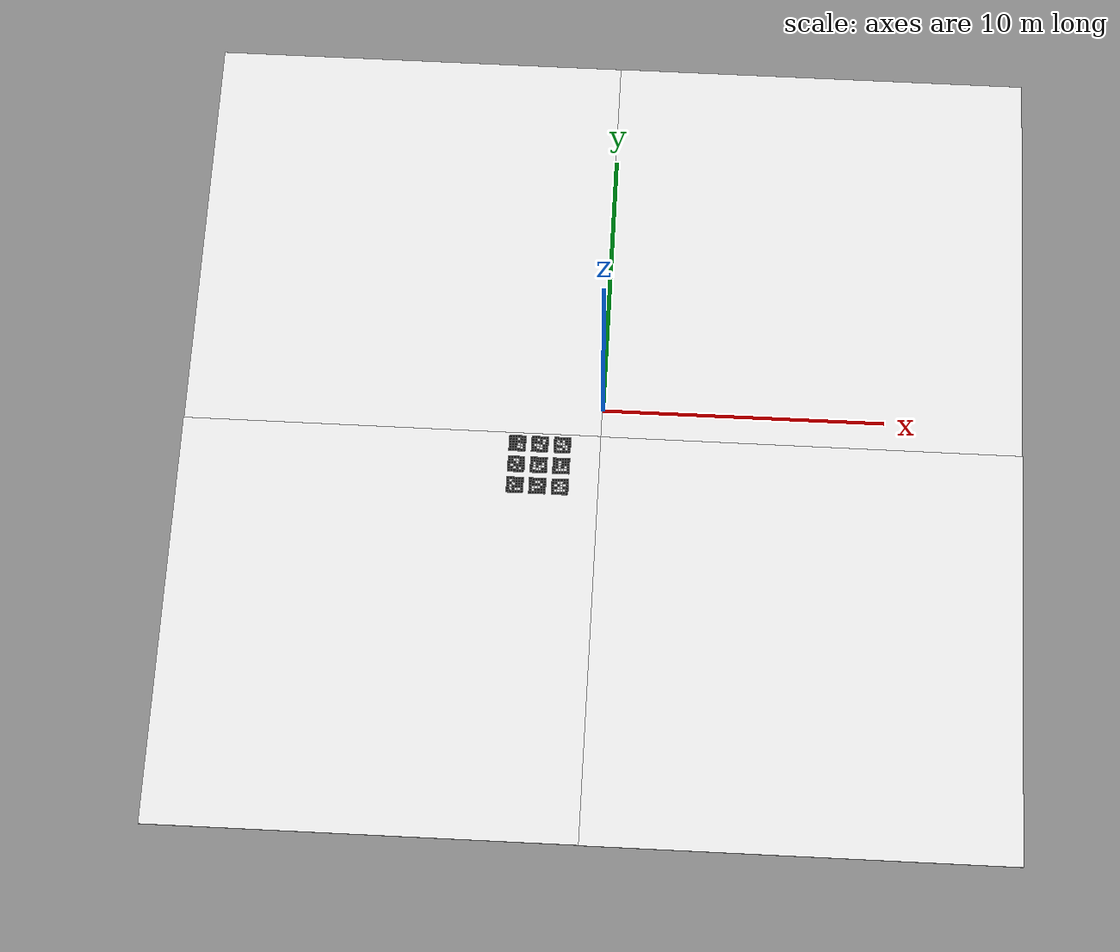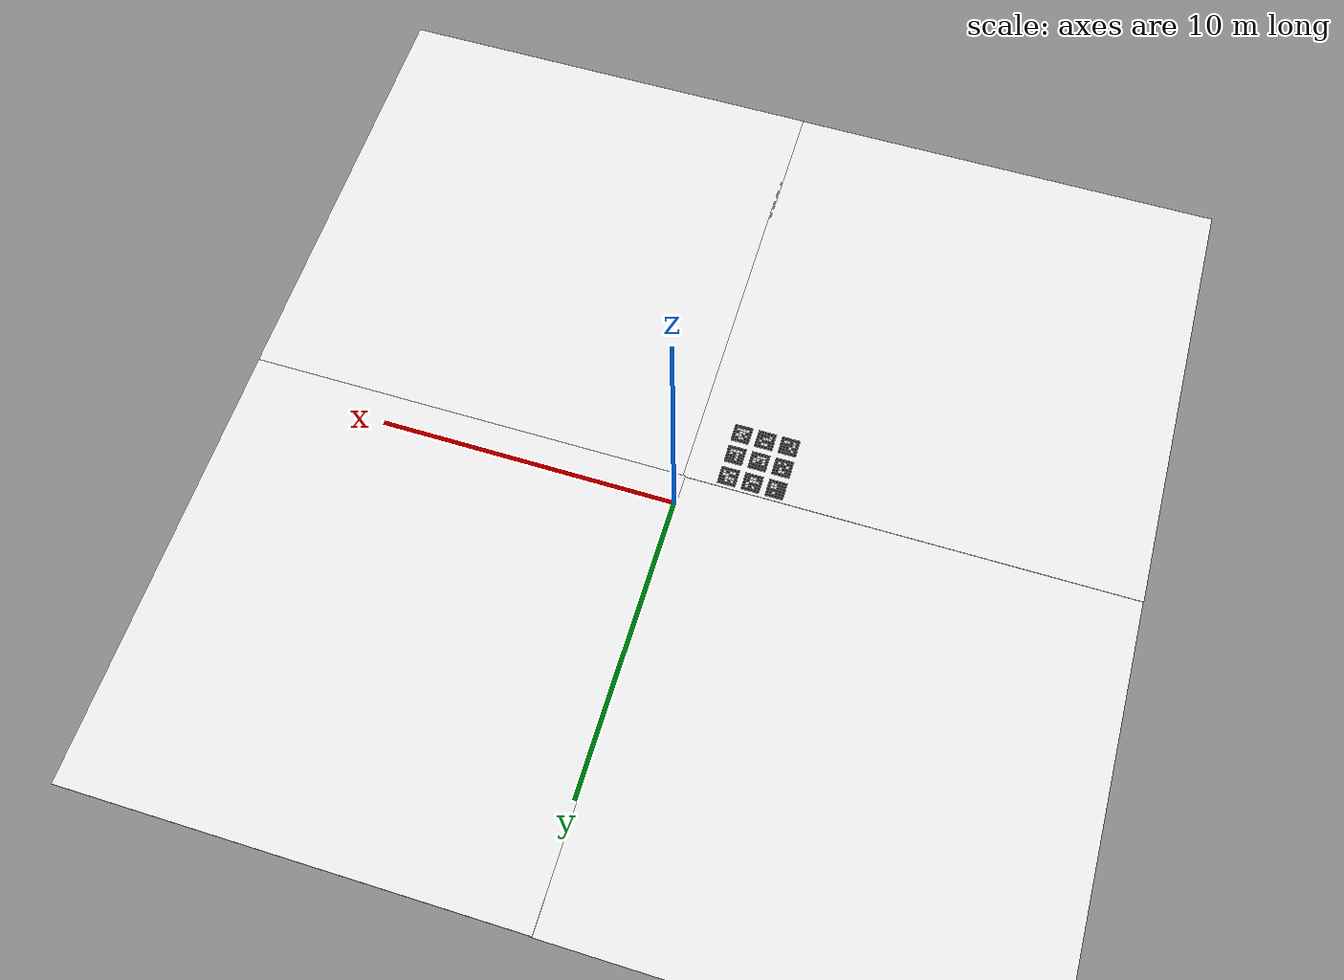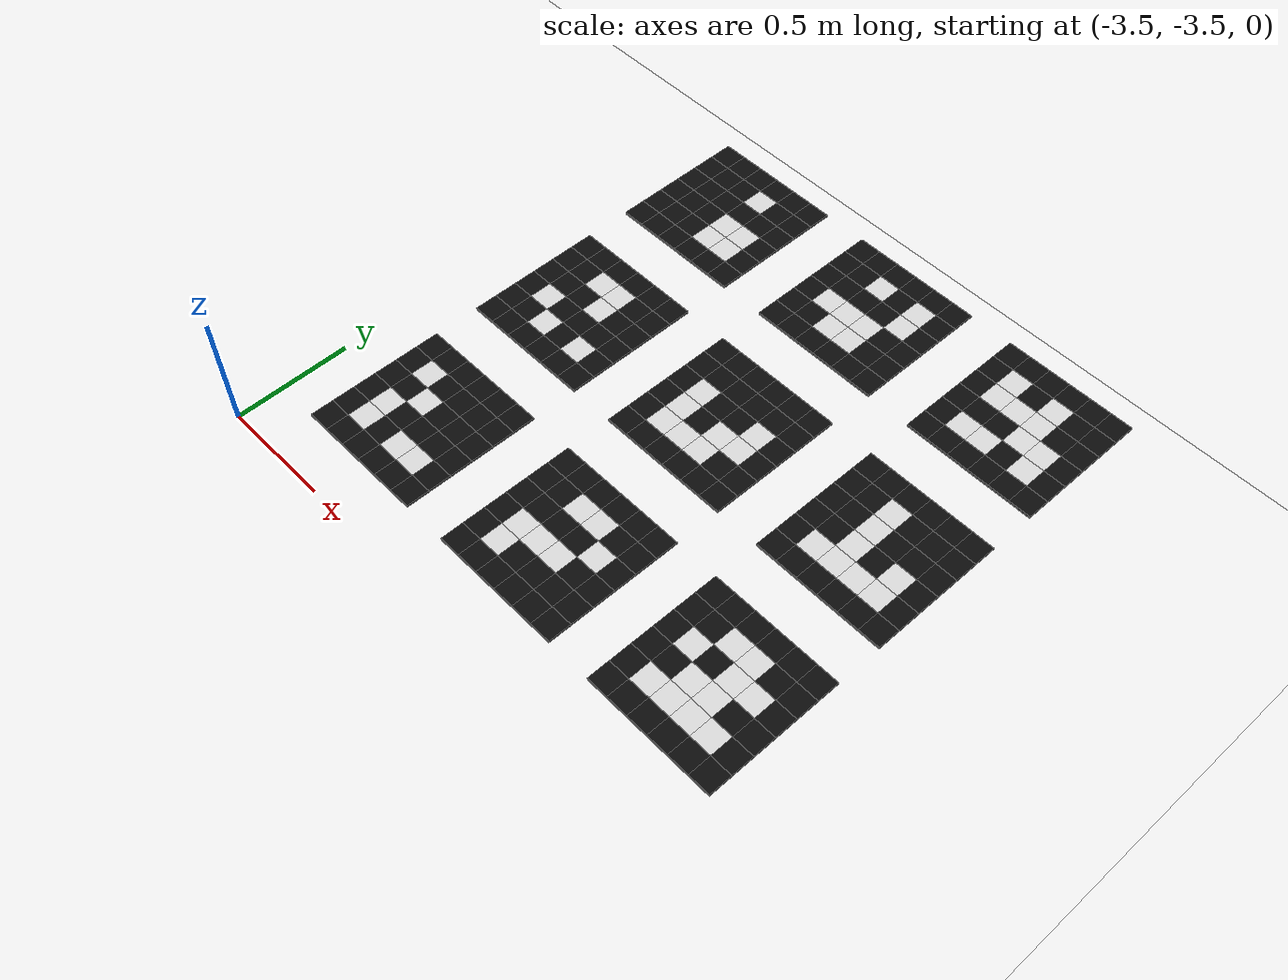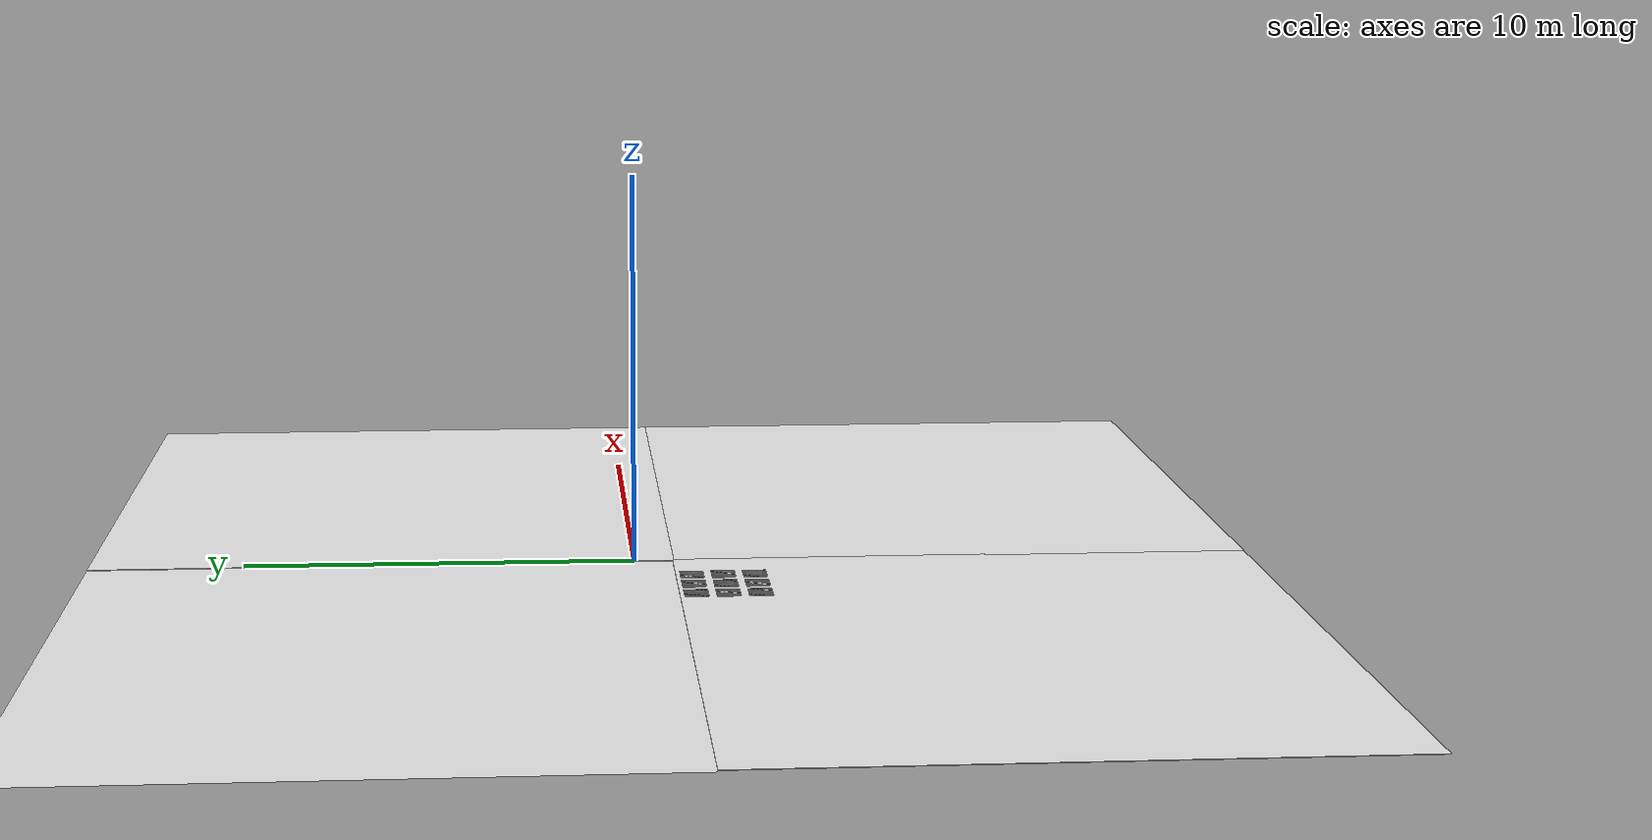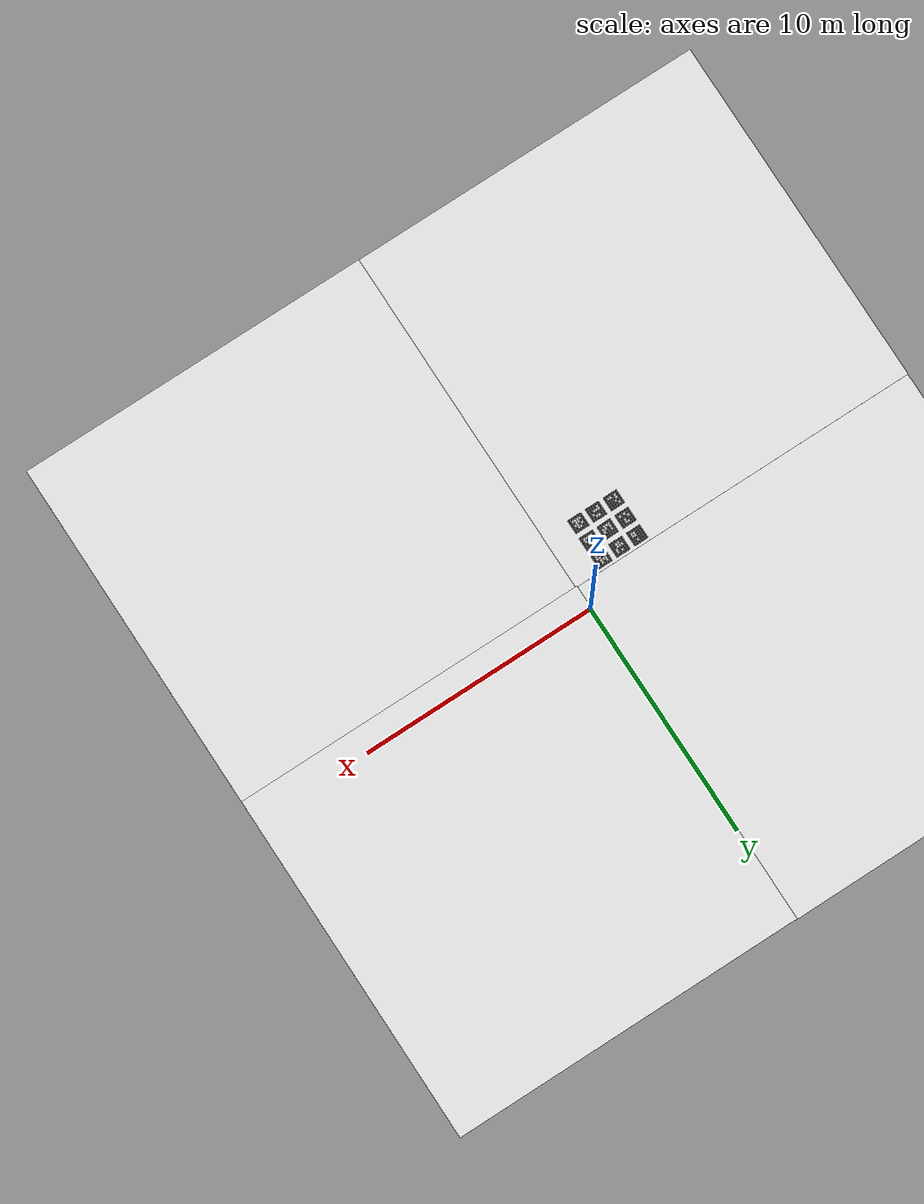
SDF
<sdf version="1.10">
 <world name="uav_world123">
  <physics name="1ms" type="ignored">
   <max_step_size>0.001</max_step_size>
   <real_time_factor>1</real_time_factor>
   <real_time_update_rate>1000</real_time_update_rate>
  </physics>
  <plugin name="gz::sim::systems::Physics" filename="gz-sim-physics-system"/>
  <plugin name="gz::sim::systems::SceneBroadcaster" filename="gz-sim-scene-broadcaster-system"/>
  <plugin name="gz::sim::systems::UserCommands" filename="gz-sim-user-commands-system"/>
  <plugin name="gz::sim::systems::Sensors" filename="gz-sim-sensors-system">
   <render_engine>ogre2</render_engine>
  </plugin>
  <gravity>0 0 -9.8000000000000007</gravity>
  <magnetic_field>5.5644999999999998e-06 2.2875799999999999e-05 -4.2388400000000002e-05</magnetic_field>
  <atmosphere type="adiabatic"/>
  <scene>
   <ambient>0.400000006 0.400000006 0.400000006 1</ambient>
   <background>0.699999988 0.699999988 0.699999988 1</background>
   <shadows>true</shadows>
  </scene>
  <model name="aruco_marker_101">
   <pose>-3 -3 0.014999999999999999 0 0 0</pose>
   <static>true</static>
   <link name="link">
    <visual name="block_0_0">
     <pose>-0.25 -0.25 0 0 0 0</pose>
     <geometry><box><size>0.10000000000000001 0.10000000000000001 0.01</size></box></geometry>
     <material>
      <ambient>0.0500000007 0.0500000007 0.0500000007 1</ambient>
      <diffuse>0.0500000007 0.0500000007 0.0500000007 1</diffuse>
     </material>
    </visual>
    <visual name="block_0_1">
     <pose>-0.15000000000000002 -0.25 0 0 0 0</pose>
     <geometry><box><size>0.10000000000000001 0.10000000000000001 0.01</size></box></geometry>
     <material>
      <ambient>0.0500000007 0.0500000007 0.0500000007 1</ambient>
      <diffuse>0.0500000007 0.0500000007 0.0500000007 1</diffuse>
     </material>
    </visual>
    <visual name="block_0_2">
     <pose>-0.050000000000000003 -0.25 0 0 0 0</pose>
     <geometry><box><size>0.10000000000000001 0.10000000000000001 0.01</size></box></geometry>
     <material>
      <ambient>0.0500000007 0.0500000007 0.0500000007 1</ambient>
      <diffuse>0.0500000007 0.0500000007 0.0500000007 1</diffuse>
     </material>
    </visual>
    <visual name="block_0_3">
     <pose>0.050000000000000003 -0.25 0 0 0 0</pose>
     <geometry><box><size>0.10000000000000001 0.10000000000000001 0.01</size></box></geometry>
     <material>
      <ambient>0.0500000007 0.0500000007 0.0500000007 1</ambient>
      <diffuse>0.0500000007 0.0500000007 0.0500000007 1</diffuse>
     </material>
    </visual>
    <visual name="block_0_4">
     <pose>0.15000000000000002 -0.25 0 0 0 0</pose>
     <geometry><box><size>0.10000000000000001 0.10000000000000001 0.01</size></box></geometry>
     <material>
      <ambient>0.0500000007 0.0500000007 0.0500000007 1</ambient>
      <diffuse>0.0500000007 0.0500000007 0.0500000007 1</diffuse>
     </material>
    </visual>
    <visual name="block_0_5">
     <pose>0.25 -0.25 0 0 0 0</pose>
     <geometry><box><size>0.10000000000000001 0.10000000000000001 0.01</size></box></geometry>
     <material>
      <ambient>0.0500000007 0.0500000007 0.0500000007 1</ambient>
      <diffuse>0.0500000007 0.0500000007 0.0500000007 1</diffuse>
     </material>
    </visual>
    <visual name="block_1_0">
     <pose>-0.25 -0.15000000000000002 0 0 0 0</pose>
     <geometry><box><size>0.10000000000000001 0.10000000000000001 0.01</size></box></geometry>
     <material>
      <ambient>0.0500000007 0.0500000007 0.0500000007 1</ambient>
      <diffuse>0.0500000007 0.0500000007 0.0500000007 1</diffuse>
     </material>
    </visual>
    <visual name="block_1_1">
     <pose>-0.15000000000000002 -0.15000000000000002 0 0 0 0</pose>
     <geometry><box><size>0.10000000000000001 0.10000000000000001 0.01</size></box></geometry>
     <material>
      <ambient>0.899999976 0.899999976 0.899999976 1</ambient>
      <diffuse>0.899999976 0.899999976 0.899999976 1</diffuse>
     </material>
    </visual>
    <visual name="block_1_2">
     <pose>-0.050000000000000003 -0.15000000000000002 0 0 0 0</pose>
     <geometry><box><size>0.10000000000000001 0.10000000000000001 0.01</size></box></geometry>
     <material>
      <ambient>0.0500000007 0.0500000007 0.0500000007 1</ambient>
      <diffuse>0.0500000007 0.0500000007 0.0500000007 1</diffuse>
     </material>
    </visual>
    <visual name="block_1_3">
     <pose>0.050000000000000003 -0.15000000000000002 0 0 0 0</pose>
     <geometry><box><size>0.10000000000000001 0.10000000000000001 0.01</size></box></geometry>
     <material>
      <ambient>0.899999976 0.899999976 0.899999976 1</ambient>
      <diffuse>0.899999976 0.899999976 0.899999976 1</diffuse>
     </material>
    </visual>
    <visual name="block_1_4">
     <pose>0.15000000000000002 -0.15000000000000002 0 0 0 0</pose>
     <geometry><box><size>0.10000000000000001 0.10000000000000001 0.01</size></box></geometry>
     <material>
      <ambient>0.899999976 0.899999976 0.899999976 1</ambient>
      <diffuse>0.899999976 0.899999976 0.899999976 1</diffuse>
     </material>
    </visual>
    <visual name="block_1_5">
     <pose>0.25 -0.15000000000000002 0 0 0 0</pose>
     <geometry><box><size>0.10000000000000001 0.10000000000000001 0.01</size></box></geometry>
     <material>
      <ambient>0.0500000007 0.0500000007 0.0500000007 1</ambient>
      <diffuse>0.0500000007 0.0500000007 0.0500000007 1</diffuse>
     </material>
    </visual>
    <visual name="block_2_0">
     <pose>-0.25 -0.050000000000000003 0 0 0 0</pose>
     <geometry><box><size>0.10000000000000001 0.10000000000000001 0.01</size></box></geometry>
     <material>
      <ambient>0.0500000007 0.0500000007 0.0500000007 1</ambient>
      <diffuse>0.0500000007 0.0500000007 0.0500000007 1</diffuse>
     </material>
    </visual>
    <visual name="block_2_1">
     <pose>-0.15000000000000002 -0.050000000000000003 0 0 0 0</pose>
     <geometry><box><size>0.10000000000000001 0.10000000000000001 0.01</size></box></geometry>
     <material>
      <ambient>0.899999976 0.899999976 0.899999976 1</ambient>
      <diffuse>0.899999976 0.899999976 0.899999976 1</diffuse>
     </material>
    </visual>
    <visual name="block_2_2">
     <pose>-0.050000000000000003 -0.050000000000000003 0 0 0 0</pose>
     <geometry><box><size>0.10000000000000001 0.10000000000000001 0.01</size></box></geometry>
     <material>
      <ambient>0.0500000007 0.0500000007 0.0500000007 1</ambient>
      <diffuse>0.0500000007 0.0500000007 0.0500000007 1</diffuse>
     </material>
    </visual>
    <visual name="block_2_3">
     <pose>0.050000000000000003 -0.050000000000000003 0 0 0 0</pose>
     <geometry><box><size>0.10000000000000001 0.10000000000000001 0.01</size></box></geometry>
     <material>
      <ambient>0.0500000007 0.0500000007 0.0500000007 1</ambient>
      <diffuse>0.0500000007 0.0500000007 0.0500000007 1</diffuse>
     </material>
    </visual>
    <visual name="block_2_4">
     <pose>0.15000000000000002 -0.050000000000000003 0 0 0 0</pose>
     <geometry><box><size>0.10000000000000001 0.10000000000000001 0.01</size></box></geometry>
     <material>
      <ambient>0.0500000007 0.0500000007 0.0500000007 1</ambient>
      <diffuse>0.0500000007 0.0500000007 0.0500000007 1</diffuse>
     </material>
    </visual>
    <visual name="block_2_5">
     <pose>0.25 -0.050000000000000003 0 0 0 0</pose>
     <geometry><box><size>0.10000000000000001 0.10000000000000001 0.01</size></box></geometry>
     <material>
      <ambient>0.0500000007 0.0500000007 0.0500000007 1</ambient>
      <diffuse>0.0500000007 0.0500000007 0.0500000007 1</diffuse>
     </material>
    </visual>
    <visual name="block_3_0">
     <pose>-0.25 0.050000000000000003 0 0 0 0</pose>
     <geometry><box><size>0.10000000000000001 0.10000000000000001 0.01</size></box></geometry>
     <material>
      <ambient>0.0500000007 0.0500000007 0.0500000007 1</ambient>
      <diffuse>0.0500000007 0.0500000007 0.0500000007 1</diffuse>
     </material>
    </visual>
    <visual name="block_3_1">
     <pose>-0.15000000000000002 0.050000000000000003 0 0 0 0</pose>
     <geometry><box><size>0.10000000000000001 0.10000000000000001 0.01</size></box></geometry>
     <material>
      <ambient>0.0500000007 0.0500000007 0.0500000007 1</ambient>
      <diffuse>0.0500000007 0.0500000007 0.0500000007 1</diffuse>
     </material>
    </visual>
    <visual name="block_3_2">
     <pose>-0.050000000000000003 0.050000000000000003 0 0 0 0</pose>
     <geometry><box><size>0.10000000000000001 0.10000000000000001 0.01</size></box></geometry>
     <material>
      <ambient>0.899999976 0.899999976 0.899999976 1</ambient>
      <diffuse>0.899999976 0.899999976 0.899999976 1</diffuse>
     </material>
    </visual>
    <visual name="block_3_3">
     <pose>0.050000000000000003 0.050000000000000003 0 0 0 0</pose>
     <geometry><box><size>0.10000000000000001 0.10000000000000001 0.01</size></box></geometry>
     <material>
      <ambient>0.0500000007 0.0500000007 0.0500000007 1</ambient>
      <diffuse>0.0500000007 0.0500000007 0.0500000007 1</diffuse>
     </material>
    </visual>
    <visual name="block_3_4">
     <pose>0.15000000000000002 0.050000000000000003 0 0 0 0</pose>
     <geometry><box><size>0.10000000000000001 0.10000000000000001 0.01</size></box></geometry>
     <material>
      <ambient>0.0500000007 0.0500000007 0.0500000007 1</ambient>
      <diffuse>0.0500000007 0.0500000007 0.0500000007 1</diffuse>
     </material>
    </visual>
    <visual name="block_3_5">
     <pose>0.25 0.050000000000000003 0 0 0 0</pose>
     <geometry><box><size>0.10000000000000001 0.10000000000000001 0.01</size></box></geometry>
     <material>
      <ambient>0.0500000007 0.0500000007 0.0500000007 1</ambient>
      <diffuse>0.0500000007 0.0500000007 0.0500000007 1</diffuse>
     </material>
    </visual>
    <visual name="block_4_0">
     <pose>-0.25 0.15000000000000002 0 0 0 0</pose>
     <geometry><box><size>0.10000000000000001 0.10000000000000001 0.01</size></box></geometry>
     <material>
      <ambient>0.0500000007 0.0500000007 0.0500000007 1</ambient>
      <diffuse>0.0500000007 0.0500000007 0.0500000007 1</diffuse>
     </material>
    </visual>
    <visual name="block_4_1">
     <pose>-0.15000000000000002 0.15000000000000002 0 0 0 0</pose>
     <geometry><box><size>0.10000000000000001 0.10000000000000001 0.01</size></box></geometry>
     <material>
      <ambient>0.899999976 0.899999976 0.899999976 1</ambient>
      <diffuse>0.899999976 0.899999976 0.899999976 1</diffuse>
     </material>
    </visual>
    <visual name="block_4_2">
     <pose>-0.050000000000000003 0.15000000000000002 0 0 0 0</pose>
     <geometry><box><size>0.10000000000000001 0.10000000000000001 0.01</size></box></geometry>
     <material>
      <ambient>0.0500000007 0.0500000007 0.0500000007 1</ambient>
      <diffuse>0.0500000007 0.0500000007 0.0500000007 1</diffuse>
     </material>
    </visual>
    <visual name="block_4_3">
     <pose>0.050000000000000003 0.15000000000000002 0 0 0 0</pose>
     <geometry><box><size>0.10000000000000001 0.10000000000000001 0.01</size></box></geometry>
     <material>
      <ambient>0.0500000007 0.0500000007 0.0500000007 1</ambient>
      <diffuse>0.0500000007 0.0500000007 0.0500000007 1</diffuse>
     </material>
    </visual>
    <visual name="block_4_4">
     <pose>0.15000000000000002 0.15000000000000002 0 0 0 0</pose>
     <geometry><box><size>0.10000000000000001 0.10000000000000001 0.01</size></box></geometry>
     <material>
      <ambient>0.0500000007 0.0500000007 0.0500000007 1</ambient>
      <diffuse>0.0500000007 0.0500000007 0.0500000007 1</diffuse>
     </material>
    </visual>
    <visual name="block_4_5">
     <pose>0.25 0.15000000000000002 0 0 0 0</pose>
     <geometry><box><size>0.10000000000000001 0.10000000000000001 0.01</size></box></geometry>
     <material>
      <ambient>0.0500000007 0.0500000007 0.0500000007 1</ambient>
      <diffuse>0.0500000007 0.0500000007 0.0500000007 1</diffuse>
     </material>
    </visual>
    <visual name="block_5_0">
     <pose>-0.25 0.25 0 0 0 0</pose>
     <geometry><box><size>0.10000000000000001 0.10000000000000001 0.01</size></box></geometry>
     <material>
      <ambient>0.0500000007 0.0500000007 0.0500000007 1</ambient>
      <diffuse>0.0500000007 0.0500000007 0.0500000007 1</diffuse>
     </material>
    </visual>
    <visual name="block_5_1">
     <pose>-0.15000000000000002 0.25 0 0 0 0</pose>
     <geometry><box><size>0.10000000000000001 0.10000000000000001 0.01</size></box></geometry>
     <material>
      <ambient>0.0500000007 0.0500000007 0.0500000007 1</ambient>
      <diffuse>0.0500000007 0.0500000007 0.0500000007 1</diffuse>
     </material>
    </visual>
    <visual name="block_5_2">
     <pose>-0.050000000000000003 0.25 0 0 0 0</pose>
     <geometry><box><size>0.10000000000000001 0.10000000000000001 0.01</size></box></geometry>
     <material>
      <ambient>0.0500000007 0.0500000007 0.0500000007 1</ambient>
      <diffuse>0.0500000007 0.0500000007 0.0500000007 1</diffuse>
     </material>
    </visual>
    <visual name="block_5_3">
     <pose>0.050000000000000003 0.25 0 0 0 0</pose>
     <geometry><box><size>0.10000000000000001 0.10000000000000001 0.01</size></box></geometry>
     <material>
      <ambient>0.0500000007 0.0500000007 0.0500000007 1</ambient>
      <diffuse>0.0500000007 0.0500000007 0.0500000007 1</diffuse>
     </material>
    </visual>
    <visual name="block_5_4">
     <pose>0.15000000000000002 0.25 0 0 0 0</pose>
     <geometry><box><size>0.10000000000000001 0.10000000000000001 0.01</size></box></geometry>
     <material>
      <ambient>0.0500000007 0.0500000007 0.0500000007 1</ambient>
      <diffuse>0.0500000007 0.0500000007 0.0500000007 1</diffuse>
     </material>
    </visual>
    <visual name="block_5_5">
     <pose>0.25 0.25 0 0 0 0</pose>
     <geometry><box><size>0.10000000000000001 0.10000000000000001 0.01</size></box></geometry>
     <material>
      <ambient>0.0500000007 0.0500000007 0.0500000007 1</ambient>
      <diffuse>0.0500000007 0.0500000007 0.0500000007 1</diffuse>
     </material>
    </visual>
    <inertial>
     <mass>1</mass>
     <inertia><ixx>1</ixx><ixy>0</ixy><ixz>0</ixz><iyy>1</iyy><iyz>0</iyz><izz>1</izz></inertia>
    </inertial>
   </link>
  </model>
  <model name="aruco_marker_102">
   <pose>-2.2000000000000002 -3 0.014999999999999999 0 0 0</pose>
   <static>true</static>
   <link name="link">
    <visual name="block_0_0">
     <pose>-0.25 -0.25 0 0 0 0</pose>
     <geometry><box><size>0.10000000000000001 0.10000000000000001 0.01</size></box></geometry>
     <material>
      <ambient>0.0500000007 0.0500000007 0.0500000007 1</ambient>
      <diffuse>0.0500000007 0.0500000007 0.0500000007 1</diffuse>
     </material>
    </visual>
    <visual name="block_0_1">
     <pose>-0.15000000000000002 -0.25 0 0 0 0</pose>
     <geometry><box><size>0.10000000000000001 0.10000000000000001 0.01</size></box></geometry>
     <material>
      <ambient>0.0500000007 0.0500000007 0.0500000007 1</ambient>
      <diffuse>0.0500000007 0.0500000007 0.0500000007 1</diffuse>
     </material>
    </visual>
    <visual name="block_0_2">
     <pose>-0.050000000000000003 -0.25 0 0 0 0</pose>
     <geometry><box><size>0.10000000000000001 0.10000000000000001 0.01</size></box></geometry>
     <material>
      <ambient>0.0500000007 0.0500000007 0.0500000007 1</ambient>
      <diffuse>0.0500000007 0.0500000007 0.0500000007 1</diffuse>
     </material>
    </visual>
    <visual name="block_0_3">
     <pose>0.050000000000000003 -0.25 0 0 0 0</pose>
     <geometry><box><size>0.10000000000000001 0.10000000000000001 0.01</size></box></geometry>
     <material>
      <ambient>0.0500000007 0.0500000007 0.0500000007 1</ambient>
      <diffuse>0.0500000007 0.0500000007 0.0500000007 1</diffuse>
     </material>
    </visual>
    <visual name="block_0_4">
     <pose>0.15000000000000002 -0.25 0 0 0 0</pose>
     <geometry><box><size>0.10000000000000001 0.10000000000000001 0.01</size></box></geometry>
     <material>
      <ambient>0.0500000007 0.0500000007 0.0500000007 1</ambient>
      <diffuse>0.0500000007 0.0500000007 0.0500000007 1</diffuse>
     </material>
    </visual>
    <visual name="block_0_5">
     <pose>0.25 -0.25 0 0 0 0</pose>
     <geometry><box><size>0.10000000000000001 0.10000000000000001 0.01</size></box></geometry>
     <material>
      <ambient>0.0500000007 0.0500000007 0.0500000007 1</ambient>
      <diffuse>0.0500000007 0.0500000007 0.0500000007 1</diffuse>
     </material>
    </visual>
    <visual name="block_1_0">
     <pose>-0.25 -0.15000000000000002 0 0 0 0</pose>
     <geometry><box><size>0.10000000000000001 0.10000000000000001 0.01</size></box></geometry>
     <material>
      <ambient>0.0500000007 0.0500000007 0.0500000007 1</ambient>
      <diffuse>0.0500000007 0.0500000007 0.0500000007 1</diffuse>
     </material>
    </visual>
    <visual name="block_1_1">
     <pose>-0.15000000000000002 -0.15000000000000002 0 0 0 0</pose>
     <geometry><box><size>0.10000000000000001 0.10000000000000001 0.01</size></box></geometry>
     <material>
      <ambient>0.899999976 0.899999976 0.899999976 1</ambient>
      <diffuse>0.899999976 0.899999976 0.899999976 1</diffuse>
     </material>
    </visual>
    <visual name="block_1_2">
     <pose>-0.050000000000000003 -0.15000000000000002 0 0 0 0</pose>
     <geometry><box><size>0.10000000000000001 0.10000000000000001 0.01</size></box></geometry>
     <material>
      <ambient>0.0500000007 0.0500000007 0.0500000007 1</ambient>
      <diffuse>0.0500000007 0.0500000007 0.0500000007 1</diffuse>
     </material>
    </visual>
    <visual name="block_1_3">
     <pose>0.050000000000000003 -0.15000000000000002 0 0 0 0</pose>
     <geometry><box><size>0.10000000000000001 0.10000000000000001 0.01</size></box></geometry>
     <material>
      <ambient>0.0500000007 0.0500000007 0.0500000007 1</ambient>
      <diffuse>0.0500000007 0.0500000007 0.0500000007 1</diffuse>
     </material>
    </visual>
    <visual name="block_1_4">
     <pose>0.15000000000000002 -0.15000000000000002 0 0 0 0</pose>
     <geometry><box><size>0.10000000000000001 0.10000000000000001 0.01</size></box></geometry>
     <material>
      <ambient>0.0500000007 0.0500000007 0.0500000007 1</ambient>
      <diffuse>0.0500000007 0.0500000007 0.0500000007 1</diffuse>
     </material>
    </visual>
    <visual name="block_1_5">
     <pose>0.25 -0.15000000000000002 0 0 0 0</pose>
     <geometry><box><size>0.10000000000000001 0.10000000000000001 0.01</size></box></geometry>
     <material>
      <ambient>0.0500000007 0.0500000007 0.0500000007 1</ambient>
      <diffuse>0.0500000007 0.0500000007 0.0500000007 1</diffuse>
     </material>
    </visual>
    <visual name="block_2_0">
     <pose>-0.25 -0.050000000000000003 0 0 0 0</pose>
     <geometry><box><size>0.10000000000000001 0.10000000000000001 0.01</size></box></geometry>
     <material>
      <ambient>0.0500000007 0.0500000007 0.0500000007 1</ambient>
      <diffuse>0.0500000007 0.0500000007 0.0500000007 1</diffuse>
     </material>
    </visual>
    <visual name="block_2_1">
     <pose>-0.15000000000000002 -0.050000000000000003 0 0 0 0</pose>
     <geometry><box><size>0.10000000000000001 0.10000000000000001 0.01</size></box></geometry>
     <material>
      <ambient>0.899999976 0.899999976 0.899999976 1</ambient>
      <diffuse>0.899999976 0.899999976 0.899999976 1</diffuse>
     </material>
    </visual>
    <visual name="block_2_2">
     <pose>-0.050000000000000003 -0.050000000000000003 0 0 0 0</pose>
     <geometry><box><size>0.10000000000000001 0.10000000000000001 0.01</size></box></geometry>
     <material>
      <ambient>0.899999976 0.899999976 0.899999976 1</ambient>
      <diffuse>0.899999976 0.899999976 0.899999976 1</diffuse>
     </material>
    </visual>
    <visual name="block_2_3">
     <pose>0.050000000000000003 -0.050000000000000003 0 0 0 0</pose>
     <geometry><box><size>0.10000000000000001 0.10000000000000001 0.01</size></box></geometry>
     <material>
      <ambient>0.899999976 0.899999976 0.899999976 1</ambient>
      <diffuse>0.899999976 0.899999976 0.899999976 1</diffuse>
     </material>
    </visual>
    <visual name="block_2_4">
     <pose>0.15000000000000002 -0.050000000000000003 0 0 0 0</pose>
     <geometry><box><size>0.10000000000000001 0.10000000000000001 0.01</size></box></geometry>
     <material>
      <ambient>0.0500000007 0.0500000007 0.0500000007 1</ambient>
      <diffuse>0.0500000007 0.0500000007 0.0500000007 1</diffuse>
     </material>
    </visual>
    <visual name="block_2_5">
     <pose>0.25 -0.050000000000000003 0 0 0 0</pose>
     <geometry><box><size>0.10000000000000001 0.10000000000000001 0.01</size></box></geometry>
     <material>
      <ambient>0.0500000007 0.0500000007 0.0500000007 1</ambient>
      <diffuse>0.0500000007 0.0500000007 0.0500000007 1</diffuse>
     </material>
    </visual>
    <visual name="block_3_0">
     <pose>-0.25 0.050000000000000003 0 0 0 0</pose>
     <geometry><box><size>0.10000000000000001 0.10000000000000001 0.01</size></box></geometry>
     <material>
      <ambient>0.0500000007 0.0500000007 0.0500000007 1</ambient>
      <diffuse>0.0500000007 0.0500000007 0.0500000007 1</diffuse>
     </material>
    </visual>
    <visual name="block_3_1">
     <pose>-0.15000000000000002 0.050000000000000003 0 0 0 0</pose>
     <geometry><box><size>0.10000000000000001 0.10000000000000001 0.01</size></box></geometry>
     <material>
      <ambient>0.0500000007 0.0500000007 0.0500000007 1</ambient>
      <diffuse>0.0500000007 0.0500000007 0.0500000007 1</diffuse>
     </material>
    </visual>
    <visual name="block_3_2">
     <pose>-0.050000000000000003 0.050000000000000003 0 0 0 0</pose>
     <geometry><box><size>0.10000000000000001 0.10000000000000001 0.01</size></box></geometry>
     <material>
      <ambient>0.0500000007 0.0500000007 0.0500000007 1</ambient>
      <diffuse>0.0500000007 0.0500000007 0.0500000007 1</diffuse>
     </material>
    </visual>
    <visual name="block_3_3">
     <pose>0.050000000000000003 0.050000000000000003 0 0 0 0</pose>
     <geometry><box><size>0.10000000000000001 0.10000000000000001 0.01</size></box></geometry>
     <material>
      <ambient>0.0500000007 0.0500000007 0.0500000007 1</ambient>
      <diffuse>0.0500000007 0.0500000007 0.0500000007 1</diffuse>
     </material>
    </visual>
    <visual name="block_3_4">
     <pose>0.15000000000000002 0.050000000000000003 0 0 0 0</pose>
     <geometry><box><size>0.10000000000000001 0.10000000000000001 0.01</size></box></geometry>
     <material>
      <ambient>0.899999976 0.899999976 0.899999976 1</ambient>
      <diffuse>0.899999976 0.899999976 0.899999976 1</diffuse>
     </material>
    </visual>
    <visual name="block_3_5">
     <pose>0.25 0.050000000000000003 0 0 0 0</pose>
     <geometry><box><size>0.10000000000000001 0.10000000000000001 0.01</size></box></geometry>
     <material>
      <ambient>0.0500000007 0.0500000007 0.0500000007 1</ambient>
      <diffuse>0.0500000007 0.0500000007 0.0500000007 1</diffuse>
     </material>
    </visual>
    <visual name="block_4_0">
     <pose>-0.25 0.15000000000000002 0 0 0 0</pose>
     <geometry><box><size>0.10000000000000001 0.10000000000000001 0.01</size></box></geometry>
     <material>
      <ambient>0.0500000007 0.0500000007 0.0500000007 1</ambient>
      <diffuse>0.0500000007 0.0500000007 0.0500000007 1</diffuse>
     </material>
    </visual>
    <visual name="block_4_1">
     <pose>-0.15000000000000002 0.15000000000000002 0 0 0 0</pose>
     <geometry><box><size>0.10000000000000001 0.10000000000000001 0.01</size></box></geometry>
     <material>
      <ambient>0.0500000007 0.0500000007 0.0500000007 1</ambient>
      <diffuse>0.0500000007 0.0500000007 0.0500000007 1</diffuse>
     </material>
    </visual>
    <visual name="block_4_2">
     <pose>-0.050000000000000003 0.15000000000000002 0 0 0 0</pose>
     <geometry><box><size>0.10000000000000001 0.10000000000000001 0.01</size></box></geometry>
     <material>
      <ambient>0.899999976 0.899999976 0.899999976 1</ambient>
      <diffuse>0.899999976 0.899999976 0.899999976 1</diffuse>
     </material>
    </visual>
    <visual name="block_4_3">
     <pose>0.050000000000000003 0.15000000000000002 0 0 0 0</pose>
     <geometry><box><size>0.10000000000000001 0.10000000000000001 0.01</size></box></geometry>
     <material>
      <ambient>0.899999976 0.899999976 0.899999976 1</ambient>
      <diffuse>0.899999976 0.899999976 0.899999976 1</diffuse>
     </material>
    </visual>
    <visual name="block_4_4">
     <pose>0.15000000000000002 0.15000000000000002 0 0 0 0</pose>
     <geometry><box><size>0.10000000000000001 0.10000000000000001 0.01</size></box></geometry>
     <material>
      <ambient>0.0500000007 0.0500000007 0.0500000007 1</ambient>
      <diffuse>0.0500000007 0.0500000007 0.0500000007 1</diffuse>
     </material>
    </visual>
    <visual name="block_4_5">
     <pose>0.25 0.15000000000000002 0 0 0 0</pose>
     <geometry><box><size>0.10000000000000001 0.10000000000000001 0.01</size></box></geometry>
     <material>
      <ambient>0.0500000007 0.0500000007 0.0500000007 1</ambient>
      <diffuse>0.0500000007 0.0500000007 0.0500000007 1</diffuse>
     </material>
    </visual>
    <visual name="block_5_0">
     <pose>-0.25 0.25 0 0 0 0</pose>
     <geometry><box><size>0.10000000000000001 0.10000000000000001 0.01</size></box></geometry>
     <material>
      <ambient>0.0500000007 0.0500000007 0.0500000007 1</ambient>
      <diffuse>0.0500000007 0.0500000007 0.0500000007 1</diffuse>
     </material>
    </visual>
    <visual name="block_5_1">
     <pose>-0.15000000000000002 0.25 0 0 0 0</pose>
     <geometry><box><size>0.10000000000000001 0.10000000000000001 0.01</size></box></geometry>
     <material>
      <ambient>0.0500000007 0.0500000007 0.0500000007 1</ambient>
      <diffuse>0.0500000007 0.0500000007 0.0500000007 1</diffuse>
     </material>
    </visual>
    <visual name="block_5_2">
     <pose>-0.050000000000000003 0.25 0 0 0 0</pose>
     <geometry><box><size>0.10000000000000001 0.10000000000000001 0.01</size></box></geometry>
     <material>
      <ambient>0.0500000007 0.0500000007 0.0500000007 1</ambient>
      <diffuse>0.0500000007 0.0500000007 0.0500000007 1</diffuse>
     </material>
    </visual>
    <visual name="block_5_3">
     <pose>0.050000000000000003 0.25 0 0 0 0</pose>
     <geometry><box><size>0.10000000000000001 0.10000000000000001 0.01</size></box></geometry>
     <material>
      <ambient>0.0500000007 0.0500000007 0.0500000007 1</ambient>
      <diffuse>0.0500000007 0.0500000007 0.0500000007 1</diffuse>
     </material>
    </visual>
    <visual name="block_5_4">
     <pose>0.15000000000000002 0.25 0 0 0 0</pose>
     <geometry><box><size>0.10000000000000001 0.10000000000000001 0.01</size></box></geometry>
     <material>
      <ambient>0.0500000007 0.0500000007 0.0500000007 1</ambient>
      <diffuse>0.0500000007 0.0500000007 0.0500000007 1</diffuse>
     </material>
    </visual>
    <visual name="block_5_5">
     <pose>0.25 0.25 0 0 0 0</pose>
     <geometry><box><size>0.10000000000000001 0.10000000000000001 0.01</size></box></geometry>
     <material>
      <ambient>0.0500000007 0.0500000007 0.0500000007 1</ambient>
      <diffuse>0.0500000007 0.0500000007 0.0500000007 1</diffuse>
     </material>
    </visual>
    <inertial>
     <mass>1</mass>
     <inertia><ixx>1</ixx><ixy>0</ixy><ixz>0</ixz><iyy>1</iyy><iyz>0</iyz><izz>1</izz></inertia>
    </inertial>
   </link>
  </model>
  <model name="aruco_marker_103">
   <pose>-1.3999999999999999 -3 0.014999999999999999 0 0 0</pose>
   <static>true</static>
   <link name="link">
    <visual name="block_0_0">
     <pose>-0.25 -0.25 0 0 0 0</pose>
     <geometry><box><size>0.10000000000000001 0.10000000000000001 0.01</size></box></geometry>
     <material>
      <ambient>0.0500000007 0.0500000007 0.0500000007 1</ambient>
      <diffuse>0.0500000007 0.0500000007 0.0500000007 1</diffuse>
     </material>
    </visual>
    <visual name="block_0_1">
     <pose>-0.15000000000000002 -0.25 0 0 0 0</pose>
     <geometry><box><size>0.10000000000000001 0.10000000000000001 0.01</size></box></geometry>
     <material>
      <ambient>0.0500000007 0.0500000007 0.0500000007 1</ambient>
      <diffuse>0.0500000007 0.0500000007 0.0500000007 1</diffuse>
     </material>
    </visual>
    <visual name="block_0_2">
     <pose>-0.050000000000000003 -0.25 0 0 0 0</pose>
     <geometry><box><size>0.10000000000000001 0.10000000000000001 0.01</size></box></geometry>
     <material>
      <ambient>0.0500000007 0.0500000007 0.0500000007 1</ambient>
      <diffuse>0.0500000007 0.0500000007 0.0500000007 1</diffuse>
     </material>
    </visual>
    <visual name="block_0_3">
     <pose>0.050000000000000003 -0.25 0 0 0 0</pose>
     <geometry><box><size>0.10000000000000001 0.10000000000000001 0.01</size></box></geometry>
     <material>
      <ambient>0.0500000007 0.0500000007 0.0500000007 1</ambient>
      <diffuse>0.0500000007 0.0500000007 0.0500000007 1</diffuse>
     </material>
    </visual>
    <visual name="block_0_4">
     <pose>0.15000000000000002 -0.25 0 0 0 0</pose>
     <geometry><box><size>0.10000000000000001 0.10000000000000001 0.01</size></box></geometry>
     <material>
      <ambient>0.0500000007 0.0500000007 0.0500000007 1</ambient>
      <diffuse>0.0500000007 0.0500000007 0.0500000007 1</diffuse>
     </material>
    </visual>
    <visual name="block_0_5">
     <pose>0.25 -0.25 0 0 0 0</pose>
     <geometry><box><size>0.10000000000000001 0.10000000000000001 0.01</size></box></geometry>
     <material>
      <ambient>0.0500000007 0.0500000007 0.0500000007 1</ambient>
      <diffuse>0.0500000007 0.0500000007 0.0500000007 1</diffuse>
     </material>
    </visual>
    <visual name="block_1_0">
     <pose>-0.25 -0.15000000000000002 0 0 0 0</pose>
     <geometry><box><size>0.10000000000000001 0.10000000000000001 0.01</size></box></geometry>
     <material>
      <ambient>0.0500000007 0.0500000007 0.0500000007 1</ambient>
      <diffuse>0.0500000007 0.0500000007 0.0500000007 1</diffuse>
     </material>
    </visual>
    <visual name="block_1_1">
     <pose>-0.15000000000000002 -0.15000000000000002 0 0 0 0</pose>
     <geometry><box><size>0.10000000000000001 0.10000000000000001 0.01</size></box></geometry>
     <material>
      <ambient>0.899999976 0.899999976 0.899999976 1</ambient>
      <diffuse>0.899999976 0.899999976 0.899999976 1</diffuse>
     </material>
    </visual>
    <visual name="block_1_2">
     <pose>-0.050000000000000003 -0.15000000000000002 0 0 0 0</pose>
     <geometry><box><size>0.10000000000000001 0.10000000000000001 0.01</size></box></geometry>
     <material>
      <ambient>0.899999976 0.899999976 0.899999976 1</ambient>
      <diffuse>0.899999976 0.899999976 0.899999976 1</diffuse>
     </material>
    </visual>
    <visual name="block_1_3">
     <pose>0.050000000000000003 -0.15000000000000002 0 0 0 0</pose>
     <geometry><box><size>0.10000000000000001 0.10000000000000001 0.01</size></box></geometry>
     <material>
      <ambient>0.899999976 0.899999976 0.899999976 1</ambient>
      <diffuse>0.899999976 0.899999976 0.899999976 1</diffuse>
     </material>
    </visual>
    <visual name="block_1_4">
     <pose>0.15000000000000002 -0.15000000000000002 0 0 0 0</pose>
     <geometry><box><size>0.10000000000000001 0.10000000000000001 0.01</size></box></geometry>
     <material>
      <ambient>0.899999976 0.899999976 0.899999976 1</ambient>
      <diffuse>0.899999976 0.899999976 0.899999976 1</diffuse>
     </material>
    </visual>
    <visual name="block_1_5">
     <pose>0.25 -0.15000000000000002 0 0 0 0</pose>
     <geometry><box><size>0.10000000000000001 0.10000000000000001 0.01</size></box></geometry>
     <material>
      <ambient>0.0500000007 0.0500000007 0.0500000007 1</ambient>
      <diffuse>0.0500000007 0.0500000007 0.0500000007 1</diffuse>
     </material>
    </visual>
    <visual name="block_2_0">
     <pose>-0.25 -0.050000000000000003 0 0 0 0</pose>
     <geometry><box><size>0.10000000000000001 0.10000000000000001 0.01</size></box></geometry>
     <material>
      <ambient>0.0500000007 0.0500000007 0.0500000007 1</ambient>
      <diffuse>0.0500000007 0.0500000007 0.0500000007 1</diffuse>
     </material>
    </visual>
    <visual name="block_2_1">
     <pose>-0.15000000000000002 -0.050000000000000003 0 0 0 0</pose>
     <geometry><box><size>0.10000000000000001 0.10000000000000001 0.01</size></box></geometry>
     <material>
      <ambient>0.0500000007 0.0500000007 0.0500000007 1</ambient>
      <diffuse>0.0500000007 0.0500000007 0.0500000007 1</diffuse>
     </material>
    </visual>
    <visual name="block_2_2">
     <pose>-0.050000000000000003 -0.050000000000000003 0 0 0 0</pose>
     <geometry><box><size>0.10000000000000001 0.10000000000000001 0.01</size></box></geometry>
     <material>
      <ambient>0.899999976 0.899999976 0.899999976 1</ambient>
      <diffuse>0.899999976 0.899999976 0.899999976 1</diffuse>
     </material>
    </visual>
    <visual name="block_2_3">
     <pose>0.050000000000000003 -0.050000000000000003 0 0 0 0</pose>
     <geometry><box><size>0.10000000000000001 0.10000000000000001 0.01</size></box></geometry>
     <material>
      <ambient>0.899999976 0.899999976 0.899999976 1</ambient>
      <diffuse>0.899999976 0.899999976 0.899999976 1</diffuse>
     </material>
    </visual>
    <visual name="block_2_4">
     <pose>0.15000000000000002 -0.050000000000000003 0 0 0 0</pose>
     <geometry><box><size>0.10000000000000001 0.10000000000000001 0.01</size></box></geometry>
     <material>
      <ambient>0.0500000007 0.0500000007 0.0500000007 1</ambient>
      <diffuse>0.0500000007 0.0500000007 0.0500000007 1</diffuse>
     </material>
    </visual>
    <visual name="block_2_5">
     <pose>0.25 -0.050000000000000003 0 0 0 0</pose>
     <geometry><box><size>0.10000000000000001 0.10000000000000001 0.01</size></box></geometry>
     <material>
      <ambient>0.0500000007 0.0500000007 0.0500000007 1</ambient>
      <diffuse>0.0500000007 0.0500000007 0.0500000007 1</diffuse>
     </material>
    </visual>
    <visual name="block_3_0">
     <pose>-0.25 0.050000000000000003 0 0 0 0</pose>
     <geometry><box><size>0.10000000000000001 0.10000000000000001 0.01</size></box></geometry>
     <material>
      <ambient>0.0500000007 0.0500000007 0.0500000007 1</ambient>
      <diffuse>0.0500000007 0.0500000007 0.0500000007 1</diffuse>
     </material>
    </visual>
    <visual name="block_3_1">
     <pose>-0.15000000000000002 0.050000000000000003 0 0 0 0</pose>
     <geometry><box><size>0.10000000000000001 0.10000000000000001 0.01</size></box></geometry>
     <material>
      <ambient>0.899999976 0.899999976 0.899999976 1</ambient>
      <diffuse>0.899999976 0.899999976 0.899999976 1</diffuse>
     </material>
    </visual>
    <visual name="block_3_2">
     <pose>-0.050000000000000003 0.050000000000000003 0 0 0 0</pose>
     <geometry><box><size>0.10000000000000001 0.10000000000000001 0.01</size></box></geometry>
     <material>
      <ambient>0.0500000007 0.0500000007 0.0500000007 1</ambient>
      <diffuse>0.0500000007 0.0500000007 0.0500000007 1</diffuse>
     </material>
    </visual>
    <visual name="block_3_3">
     <pose>0.050000000000000003 0.050000000000000003 0 0 0 0</pose>
     <geometry><box><size>0.10000000000000001 0.10000000000000001 0.01</size></box></geometry>
     <material>
      <ambient>0.899999976 0.899999976 0.899999976 1</ambient>
      <diffuse>0.899999976 0.899999976 0.899999976 1</diffuse>
     </material>
    </visual>
    <visual name="block_3_4">
     <pose>0.15000000000000002 0.050000000000000003 0 0 0 0</pose>
     <geometry><box><size>0.10000000000000001 0.10000000000000001 0.01</size></box></geometry>
     <material>
      <ambient>0.899999976 0.899999976 0.899999976 1</ambient>
      <diffuse>0.899999976 0.899999976 0.899999976 1</diffuse>
     </material>
    </visual>
    <visual name="block_3_5">
     <pose>0.25 0.050000000000000003 0 0 0 0</pose>
     <geometry><box><size>0.10000000000000001 0.10000000000000001 0.01</size></box></geometry>
     <material>
      <ambient>0.0500000007 0.0500000007 0.0500000007 1</ambient>
      <diffuse>0.0500000007 0.0500000007 0.0500000007 1</diffuse>
     </material>
    </visual>
    <visual name="block_4_0">
     <pose>-0.25 0.15000000000000002 0 0 0 0</pose>
     <geometry><box><size>0.10000000000000001 0.10000000000000001 0.01</size></box></geometry>
     <material>
      <ambient>0.0500000007 0.0500000007 0.0500000007 1</ambient>
      <diffuse>0.0500000007 0.0500000007 0.0500000007 1</diffuse>
     </material>
    </visual>
    <visual name="block_4_1">
     <pose>-0.15000000000000002 0.15000000000000002 0 0 0 0</pose>
     <geometry><box><size>0.10000000000000001 0.10000000000000001 0.01</size></box></geometry>
     <material>
      <ambient>0.0500000007 0.0500000007 0.0500000007 1</ambient>
      <diffuse>0.0500000007 0.0500000007 0.0500000007 1</diffuse>
     </material>
    </visual>
    <visual name="block_4_2">
     <pose>-0.050000000000000003 0.15000000000000002 0 0 0 0</pose>
     <geometry><box><size>0.10000000000000001 0.10000000000000001 0.01</size></box></geometry>
     <material>
      <ambient>0.899999976 0.899999976 0.899999976 1</ambient>
      <diffuse>0.899999976 0.899999976 0.899999976 1</diffuse>
     </material>
    </visual>
    <visual name="block_4_3">
     <pose>0.050000000000000003 0.15000000000000002 0 0 0 0</pose>
     <geometry><box><size>0.10000000000000001 0.10000000000000001 0.01</size></box></geometry>
     <material>
      <ambient>0.899999976 0.899999976 0.899999976 1</ambient>
      <diffuse>0.899999976 0.899999976 0.899999976 1</diffuse>
     </material>
    </visual>
    <visual name="block_4_4">
     <pose>0.15000000000000002 0.15000000000000002 0 0 0 0</pose>
     <geometry><box><size>0.10000000000000001 0.10000000000000001 0.01</size></box></geometry>
     <material>
      <ambient>0.0500000007 0.0500000007 0.0500000007 1</ambient>
      <diffuse>0.0500000007 0.0500000007 0.0500000007 1</diffuse>
     </material>
    </visual>
    <visual name="block_4_5">
     <pose>0.25 0.15000000000000002 0 0 0 0</pose>
     <geometry><box><size>0.10000000000000001 0.10000000000000001 0.01</size></box></geometry>
     <material>
      <ambient>0.0500000007 0.0500000007 0.0500000007 1</ambient>
      <diffuse>0.0500000007 0.0500000007 0.0500000007 1</diffuse>
     </material>
    </visual>
    <visual name="block_5_0">
     <pose>-0.25 0.25 0 0 0 0</pose>
     <geometry><box><size>0.10000000000000001 0.10000000000000001 0.01</size></box></geometry>
     <material>
      <ambient>0.0500000007 0.0500000007 0.0500000007 1</ambient>
      <diffuse>0.0500000007 0.0500000007 0.0500000007 1</diffuse>
     </material>
    </visual>
    <visual name="block_5_1">
     <pose>-0.15000000000000002 0.25 0 0 0 0</pose>
     <geometry><box><size>0.10000000000000001 0.10000000000000001 0.01</size></box></geometry>
     <material>
      <ambient>0.0500000007 0.0500000007 0.0500000007 1</ambient>
      <diffuse>0.0500000007 0.0500000007 0.0500000007 1</diffuse>
     </material>
    </visual>
    <visual name="block_5_2">
     <pose>-0.050000000000000003 0.25 0 0 0 0</pose>
     <geometry><box><size>0.10000000000000001 0.10000000000000001 0.01</size></box></geometry>
     <material>
      <ambient>0.0500000007 0.0500000007 0.0500000007 1</ambient>
      <diffuse>0.0500000007 0.0500000007 0.0500000007 1</diffuse>
     </material>
    </visual>
    <visual name="block_5_3">
     <pose>0.050000000000000003 0.25 0 0 0 0</pose>
     <geometry><box><size>0.10000000000000001 0.10000000000000001 0.01</size></box></geometry>
     <material>
      <ambient>0.0500000007 0.0500000007 0.0500000007 1</ambient>
      <diffuse>0.0500000007 0.0500000007 0.0500000007 1</diffuse>
     </material>
    </visual>
    <visual name="block_5_4">
     <pose>0.15000000000000002 0.25 0 0 0 0</pose>
     <geometry><box><size>0.10000000000000001 0.10000000000000001 0.01</size></box></geometry>
     <material>
      <ambient>0.0500000007 0.0500000007 0.0500000007 1</ambient>
      <diffuse>0.0500000007 0.0500000007 0.0500000007 1</diffuse>
     </material>
    </visual>
    <visual name="block_5_5">
     <pose>0.25 0.25 0 0 0 0</pose>
     <geometry><box><size>0.10000000000000001 0.10000000000000001 0.01</size></box></geometry>
     <material>
      <ambient>0.0500000007 0.0500000007 0.0500000007 1</ambient>
      <diffuse>0.0500000007 0.0500000007 0.0500000007 1</diffuse>
     </material>
    </visual>
    <inertial>
     <mass>1</mass>
     <inertia><ixx>1</ixx><ixy>0</ixy><ixz>0</ixz><iyy>1</iyy><iyz>0</iyz><izz>1</izz></inertia>
    </inertial>
   </link>
  </model>
  <model name="aruco_marker_104">
   <pose>-3 -2.2000000000000002 0.014999999999999999 0 0 0</pose>
   <static>true</static>
   <link name="link">
    <visual name="block_0_0">
     <pose>-0.25 -0.25 0 0 0 0</pose>
     <geometry><box><size>0.10000000000000001 0.10000000000000001 0.01</size></box></geometry>
     <material>
      <ambient>0.0500000007 0.0500000007 0.0500000007 1</ambient>
      <diffuse>0.0500000007 0.0500000007 0.0500000007 1</diffuse>
     </material>
    </visual>
    <visual name="block_0_1">
     <pose>-0.15000000000000002 -0.25 0 0 0 0</pose>
     <geometry><box><size>0.10000000000000001 0.10000000000000001 0.01</size></box></geometry>
     <material>
      <ambient>0.0500000007 0.0500000007 0.0500000007 1</ambient>
      <diffuse>0.0500000007 0.0500000007 0.0500000007 1</diffuse>
     </material>
    </visual>
    <visual name="block_0_2">
     <pose>-0.050000000000000003 -0.25 0 0 0 0</pose>
     <geometry><box><size>0.10000000000000001 0.10000000000000001 0.01</size></box></geometry>
     <material>
      <ambient>0.0500000007 0.0500000007 0.0500000007 1</ambient>
      <diffuse>0.0500000007 0.0500000007 0.0500000007 1</diffuse>
     </material>
    </visual>
    <visual name="block_0_3">
     <pose>0.050000000000000003 -0.25 0 0 0 0</pose>
     <geometry><box><size>0.10000000000000001 0.10000000000000001 0.01</size></box></geometry>
     <material>
      <ambient>0.0500000007 0.0500000007 0.0500000007 1</ambient>
      <diffuse>0.0500000007 0.0500000007 0.0500000007 1</diffuse>
     </material>
    </visual>
    <visual name="block_0_4">
     <pose>0.15000000000000002 -0.25 0 0 0 0</pose>
     <geometry><box><size>0.10000000000000001 0.10000000000000001 0.01</size></box></geometry>
     <material>
      <ambient>0.0500000007 0.0500000007 0.0500000007 1</ambient>
      <diffuse>0.0500000007 0.0500000007 0.0500000007 1</diffuse>
     </material>
    </visual>
    <visual name="block_0_5">
     <pose>0.25 -0.25 0 0 0 0</pose>
     <geometry><box><size>0.10000000000000001 0.10000000000000001 0.01</size></box></geometry>
     <material>
      <ambient>0.0500000007 0.0500000007 0.0500000007 1</ambient>
      <diffuse>0.0500000007 0.0500000007 0.0500000007 1</diffuse>
     </material>
    </visual>
    <visual name="block_1_0">
     <pose>-0.25 -0.15000000000000002 0 0 0 0</pose>
     <geometry><box><size>0.10000000000000001 0.10000000000000001 0.01</size></box></geometry>
     <material>
      <ambient>0.0500000007 0.0500000007 0.0500000007 1</ambient>
      <diffuse>0.0500000007 0.0500000007 0.0500000007 1</diffuse>
     </material>
    </visual>
    <visual name="block_1_1">
     <pose>-0.15000000000000002 -0.15000000000000002 0 0 0 0</pose>
     <geometry><box><size>0.10000000000000001 0.10000000000000001 0.01</size></box></geometry>
     <material>
      <ambient>0.0500000007 0.0500000007 0.0500000007 1</ambient>
      <diffuse>0.0500000007 0.0500000007 0.0500000007 1</diffuse>
     </material>
    </visual>
    <visual name="block_1_2">
     <pose>-0.050000000000000003 -0.15000000000000002 0 0 0 0</pose>
     <geometry><box><size>0.10000000000000001 0.10000000000000001 0.01</size></box></geometry>
     <material>
      <ambient>0.899999976 0.899999976 0.899999976 1</ambient>
      <diffuse>0.899999976 0.899999976 0.899999976 1</diffuse>
     </material>
    </visual>
    <visual name="block_1_3">
     <pose>0.050000000000000003 -0.15000000000000002 0 0 0 0</pose>
     <geometry><box><size>0.10000000000000001 0.10000000000000001 0.01</size></box></geometry>
     <material>
      <ambient>0.0500000007 0.0500000007 0.0500000007 1</ambient>
      <diffuse>0.0500000007 0.0500000007 0.0500000007 1</diffuse>
     </material>
    </visual>
    <visual name="block_1_4">
     <pose>0.15000000000000002 -0.15000000000000002 0 0 0 0</pose>
     <geometry><box><size>0.10000000000000001 0.10000000000000001 0.01</size></box></geometry>
     <material>
      <ambient>0.899999976 0.899999976 0.899999976 1</ambient>
      <diffuse>0.899999976 0.899999976 0.899999976 1</diffuse>
     </material>
    </visual>
    <visual name="block_1_5">
     <pose>0.25 -0.15000000000000002 0 0 0 0</pose>
     <geometry><box><size>0.10000000000000001 0.10000000000000001 0.01</size></box></geometry>
     <material>
      <ambient>0.0500000007 0.0500000007 0.0500000007 1</ambient>
      <diffuse>0.0500000007 0.0500000007 0.0500000007 1</diffuse>
     </material>
    </visual>
    <visual name="block_2_0">
     <pose>-0.25 -0.050000000000000003 0 0 0 0</pose>
     <geometry><box><size>0.10000000000000001 0.10000000000000001 0.01</size></box></geometry>
     <material>
      <ambient>0.0500000007 0.0500000007 0.0500000007 1</ambient>
      <diffuse>0.0500000007 0.0500000007 0.0500000007 1</diffuse>
     </material>
    </visual>
    <visual name="block_2_1">
     <pose>-0.15000000000000002 -0.050000000000000003 0 0 0 0</pose>
     <geometry><box><size>0.10000000000000001 0.10000000000000001 0.01</size></box></geometry>
     <material>
      <ambient>0.899999976 0.899999976 0.899999976 1</ambient>
      <diffuse>0.899999976 0.899999976 0.899999976 1</diffuse>
     </material>
    </visual>
    <visual name="block_2_2">
     <pose>-0.050000000000000003 -0.050000000000000003 0 0 0 0</pose>
     <geometry><box><size>0.10000000000000001 0.10000000000000001 0.01</size></box></geometry>
     <material>
      <ambient>0.0500000007 0.0500000007 0.0500000007 1</ambient>
      <diffuse>0.0500000007 0.0500000007 0.0500000007 1</diffuse>
     </material>
    </visual>
    <visual name="block_2_3">
     <pose>0.050000000000000003 -0.050000000000000003 0 0 0 0</pose>
     <geometry><box><size>0.10000000000000001 0.10000000000000001 0.01</size></box></geometry>
     <material>
      <ambient>0.0500000007 0.0500000007 0.0500000007 1</ambient>
      <diffuse>0.0500000007 0.0500000007 0.0500000007 1</diffuse>
     </material>
    </visual>
    <visual name="block_2_4">
     <pose>0.15000000000000002 -0.050000000000000003 0 0 0 0</pose>
     <geometry><box><size>0.10000000000000001 0.10000000000000001 0.01</size></box></geometry>
     <material>
      <ambient>0.0500000007 0.0500000007 0.0500000007 1</ambient>
      <diffuse>0.0500000007 0.0500000007 0.0500000007 1</diffuse>
     </material>
    </visual>
    <visual name="block_2_5">
     <pose>0.25 -0.050000000000000003 0 0 0 0</pose>
     <geometry><box><size>0.10000000000000001 0.10000000000000001 0.01</size></box></geometry>
     <material>
      <ambient>0.0500000007 0.0500000007 0.0500000007 1</ambient>
      <diffuse>0.0500000007 0.0500000007 0.0500000007 1</diffuse>
     </material>
    </visual>
    <visual name="block_3_0">
     <pose>-0.25 0.050000000000000003 0 0 0 0</pose>
     <geometry><box><size>0.10000000000000001 0.10000000000000001 0.01</size></box></geometry>
     <material>
      <ambient>0.0500000007 0.0500000007 0.0500000007 1</ambient>
      <diffuse>0.0500000007 0.0500000007 0.0500000007 1</diffuse>
     </material>
    </visual>
    <visual name="block_3_1">
     <pose>-0.15000000000000002 0.050000000000000003 0 0 0 0</pose>
     <geometry><box><size>0.10000000000000001 0.10000000000000001 0.01</size></box></geometry>
     <material>
      <ambient>0.0500000007 0.0500000007 0.0500000007 1</ambient>
      <diffuse>0.0500000007 0.0500000007 0.0500000007 1</diffuse>
     </material>
    </visual>
    <visual name="block_3_2">
     <pose>-0.050000000000000003 0.050000000000000003 0 0 0 0</pose>
     <geometry><box><size>0.10000000000000001 0.10000000000000001 0.01</size></box></geometry>
     <material>
      <ambient>0.0500000007 0.0500000007 0.0500000007 1</ambient>
      <diffuse>0.0500000007 0.0500000007 0.0500000007 1</diffuse>
     </material>
    </visual>
    <visual name="block_3_3">
     <pose>0.050000000000000003 0.050000000000000003 0 0 0 0</pose>
     <geometry><box><size>0.10000000000000001 0.10000000000000001 0.01</size></box></geometry>
     <material>
      <ambient>0.899999976 0.899999976 0.899999976 1</ambient>
      <diffuse>0.899999976 0.899999976 0.899999976 1</diffuse>
     </material>
    </visual>
    <visual name="block_3_4">
     <pose>0.15000000000000002 0.050000000000000003 0 0 0 0</pose>
     <geometry><box><size>0.10000000000000001 0.10000000000000001 0.01</size></box></geometry>
     <material>
      <ambient>0.0500000007 0.0500000007 0.0500000007 1</ambient>
      <diffuse>0.0500000007 0.0500000007 0.0500000007 1</diffuse>
     </material>
    </visual>
    <visual name="block_3_5">
     <pose>0.25 0.050000000000000003 0 0 0 0</pose>
     <geometry><box><size>0.10000000000000001 0.10000000000000001 0.01</size></box></geometry>
     <material>
      <ambient>0.0500000007 0.0500000007 0.0500000007 1</ambient>
      <diffuse>0.0500000007 0.0500000007 0.0500000007 1</diffuse>
     </material>
    </visual>
    <visual name="block_4_0">
     <pose>-0.25 0.15000000000000002 0 0 0 0</pose>
     <geometry><box><size>0.10000000000000001 0.10000000000000001 0.01</size></box></geometry>
     <material>
      <ambient>0.0500000007 0.0500000007 0.0500000007 1</ambient>
      <diffuse>0.0500000007 0.0500000007 0.0500000007 1</diffuse>
     </material>
    </visual>
    <visual name="block_4_1">
     <pose>-0.15000000000000002 0.15000000000000002 0 0 0 0</pose>
     <geometry><box><size>0.10000000000000001 0.10000000000000001 0.01</size></box></geometry>
     <material>
      <ambient>0.0500000007 0.0500000007 0.0500000007 1</ambient>
      <diffuse>0.0500000007 0.0500000007 0.0500000007 1</diffuse>
     </material>
    </visual>
    <visual name="block_4_2">
     <pose>-0.050000000000000003 0.15000000000000002 0 0 0 0</pose>
     <geometry><box><size>0.10000000000000001 0.10000000000000001 0.01</size></box></geometry>
     <material>
      <ambient>0.899999976 0.899999976 0.899999976 1</ambient>
      <diffuse>0.899999976 0.899999976 0.899999976 1</diffuse>
     </material>
    </visual>
    <visual name="block_4_3">
     <pose>0.050000000000000003 0.15000000000000002 0 0 0 0</pose>
     <geometry><box><size>0.10000000000000001 0.10000000000000001 0.01</size></box></geometry>
     <material>
      <ambient>0.899999976 0.899999976 0.899999976 1</ambient>
      <diffuse>0.899999976 0.899999976 0.899999976 1</diffuse>
     </material>
    </visual>
    <visual name="block_4_4">
     <pose>0.15000000000000002 0.15000000000000002 0 0 0 0</pose>
     <geometry><box><size>0.10000000000000001 0.10000000000000001 0.01</size></box></geometry>
     <material>
      <ambient>0.0500000007 0.0500000007 0.0500000007 1</ambient>
      <diffuse>0.0500000007 0.0500000007 0.0500000007 1</diffuse>
     </material>
    </visual>
    <visual name="block_4_5">
     <pose>0.25 0.15000000000000002 0 0 0 0</pose>
     <geometry><box><size>0.10000000000000001 0.10000000000000001 0.01</size></box></geometry>
     <material>
      <ambient>0.0500000007 0.0500000007 0.0500000007 1</ambient>
      <diffuse>0.0500000007 0.0500000007 0.0500000007 1</diffuse>
     </material>
    </visual>
    <visual name="block_5_0">
     <pose>-0.25 0.25 0 0 0 0</pose>
     <geometry><box><size>0.10000000000000001 0.10000000000000001 0.01</size></box></geometry>
     <material>
      <ambient>0.0500000007 0.0500000007 0.0500000007 1</ambient>
      <diffuse>0.0500000007 0.0500000007 0.0500000007 1</diffuse>
     </material>
    </visual>
    <visual name="block_5_1">
     <pose>-0.15000000000000002 0.25 0 0 0 0</pose>
     <geometry><box><size>0.10000000000000001 0.10000000000000001 0.01</size></box></geometry>
     <material>
      <ambient>0.0500000007 0.0500000007 0.0500000007 1</ambient>
      <diffuse>0.0500000007 0.0500000007 0.0500000007 1</diffuse>
     </material>
    </visual>
    <visual name="block_5_2">
     <pose>-0.050000000000000003 0.25 0 0 0 0</pose>
     <geometry><box><size>0.10000000000000001 0.10000000000000001 0.01</size></box></geometry>
     <material>
      <ambient>0.0500000007 0.0500000007 0.0500000007 1</ambient>
      <diffuse>0.0500000007 0.0500000007 0.0500000007 1</diffuse>
     </material>
    </visual>
    <visual name="block_5_3">
     <pose>0.050000000000000003 0.25 0 0 0 0</pose>
     <geometry><box><size>0.10000000000000001 0.10000000000000001 0.01</size></box></geometry>
     <material>
      <ambient>0.0500000007 0.0500000007 0.0500000007 1</ambient>
      <diffuse>0.0500000007 0.0500000007 0.0500000007 1</diffuse>
     </material>
    </visual>
    <visual name="block_5_4">
     <pose>0.15000000000000002 0.25 0 0 0 0</pose>
     <geometry><box><size>0.10000000000000001 0.10000000000000001 0.01</size></box></geometry>
     <material>
      <ambient>0.0500000007 0.0500000007 0.0500000007 1</ambient>
      <diffuse>0.0500000007 0.0500000007 0.0500000007 1</diffuse>
     </material>
    </visual>
    <visual name="block_5_5">
     <pose>0.25 0.25 0 0 0 0</pose>
     <geometry><box><size>0.10000000000000001 0.10000000000000001 0.01</size></box></geometry>
     <material>
      <ambient>0.0500000007 0.0500000007 0.0500000007 1</ambient>
      <diffuse>0.0500000007 0.0500000007 0.0500000007 1</diffuse>
     </material>
    </visual>
    <inertial>
     <mass>1</mass>
     <inertia><ixx>1</ixx><ixy>0</ixy><ixz>0</ixz><iyy>1</iyy><iyz>0</iyz><izz>1</izz></inertia>
    </inertial>
   </link>
  </model>
  <model name="aruco_marker_105">
   <pose>-2.2000000000000002 -2.2000000000000002 0.014999999999999999 0 0 0</pose>
   <static>true</static>
   <link name="link">
    <visual name="block_0_0">
     <pose>-0.25 -0.25 0 0 0 0</pose>
     <geometry><box><size>0.10000000000000001 0.10000000000000001 0.01</size></box></geometry>
     <material>
      <ambient>0.0500000007 0.0500000007 0.0500000007 1</ambient>
      <diffuse>0.0500000007 0.0500000007 0.0500000007 1</diffuse>
     </material>
    </visual>
    <visual name="block_0_1">
     <pose>-0.15000000000000002 -0.25 0 0 0 0</pose>
     <geometry><box><size>0.10000000000000001 0.10000000000000001 0.01</size></box></geometry>
     <material>
      <ambient>0.0500000007 0.0500000007 0.0500000007 1</ambient>
      <diffuse>0.0500000007 0.0500000007 0.0500000007 1</diffuse>
     </material>
    </visual>
    <visual name="block_0_2">
     <pose>-0.050000000000000003 -0.25 0 0 0 0</pose>
     <geometry><box><size>0.10000000000000001 0.10000000000000001 0.01</size></box></geometry>
     <material>
      <ambient>0.0500000007 0.0500000007 0.0500000007 1</ambient>
      <diffuse>0.0500000007 0.0500000007 0.0500000007 1</diffuse>
     </material>
    </visual>
    <visual name="block_0_3">
     <pose>0.050000000000000003 -0.25 0 0 0 0</pose>
     <geometry><box><size>0.10000000000000001 0.10000000000000001 0.01</size></box></geometry>
     <material>
      <ambient>0.0500000007 0.0500000007 0.0500000007 1</ambient>
      <diffuse>0.0500000007 0.0500000007 0.0500000007 1</diffuse>
     </material>
    </visual>
    <visual name="block_0_4">
     <pose>0.15000000000000002 -0.25 0 0 0 0</pose>
     <geometry><box><size>0.10000000000000001 0.10000000000000001 0.01</size></box></geometry>
     <material>
      <ambient>0.0500000007 0.0500000007 0.0500000007 1</ambient>
      <diffuse>0.0500000007 0.0500000007 0.0500000007 1</diffuse>
     </material>
    </visual>
    <visual name="block_0_5">
     <pose>0.25 -0.25 0 0 0 0</pose>
     <geometry><box><size>0.10000000000000001 0.10000000000000001 0.01</size></box></geometry>
     <material>
      <ambient>0.0500000007 0.0500000007 0.0500000007 1</ambient>
      <diffuse>0.0500000007 0.0500000007 0.0500000007 1</diffuse>
     </material>
    </visual>
    <visual name="block_1_0">
     <pose>-0.25 -0.15000000000000002 0 0 0 0</pose>
     <geometry><box><size>0.10000000000000001 0.10000000000000001 0.01</size></box></geometry>
     <material>
      <ambient>0.0500000007 0.0500000007 0.0500000007 1</ambient>
      <diffuse>0.0500000007 0.0500000007 0.0500000007 1</diffuse>
     </material>
    </visual>
    <visual name="block_1_1">
     <pose>-0.15000000000000002 -0.15000000000000002 0 0 0 0</pose>
     <geometry><box><size>0.10000000000000001 0.10000000000000001 0.01</size></box></geometry>
     <material>
      <ambient>0.899999976 0.899999976 0.899999976 1</ambient>
      <diffuse>0.899999976 0.899999976 0.899999976 1</diffuse>
     </material>
    </visual>
    <visual name="block_1_2">
     <pose>-0.050000000000000003 -0.15000000000000002 0 0 0 0</pose>
     <geometry><box><size>0.10000000000000001 0.10000000000000001 0.01</size></box></geometry>
     <material>
      <ambient>0.899999976 0.899999976 0.899999976 1</ambient>
      <diffuse>0.899999976 0.899999976 0.899999976 1</diffuse>
     </material>
    </visual>
    <visual name="block_1_3">
     <pose>0.050000000000000003 -0.15000000000000002 0 0 0 0</pose>
     <geometry><box><size>0.10000000000000001 0.10000000000000001 0.01</size></box></geometry>
     <material>
      <ambient>0.899999976 0.899999976 0.899999976 1</ambient>
      <diffuse>0.899999976 0.899999976 0.899999976 1</diffuse>
     </material>
    </visual>
    <visual name="block_1_4">
     <pose>0.15000000000000002 -0.15000000000000002 0 0 0 0</pose>
     <geometry><box><size>0.10000000000000001 0.10000000000000001 0.01</size></box></geometry>
     <material>
      <ambient>0.0500000007 0.0500000007 0.0500000007 1</ambient>
      <diffuse>0.0500000007 0.0500000007 0.0500000007 1</diffuse>
     </material>
    </visual>
    <visual name="block_1_5">
     <pose>0.25 -0.15000000000000002 0 0 0 0</pose>
     <geometry><box><size>0.10000000000000001 0.10000000000000001 0.01</size></box></geometry>
     <material>
      <ambient>0.0500000007 0.0500000007 0.0500000007 1</ambient>
      <diffuse>0.0500000007 0.0500000007 0.0500000007 1</diffuse>
     </material>
    </visual>
    <visual name="block_2_0">
     <pose>-0.25 -0.050000000000000003 0 0 0 0</pose>
     <geometry><box><size>0.10000000000000001 0.10000000000000001 0.01</size></box></geometry>
     <material>
      <ambient>0.0500000007 0.0500000007 0.0500000007 1</ambient>
      <diffuse>0.0500000007 0.0500000007 0.0500000007 1</diffuse>
     </material>
    </visual>
    <visual name="block_2_1">
     <pose>-0.15000000000000002 -0.050000000000000003 0 0 0 0</pose>
     <geometry><box><size>0.10000000000000001 0.10000000000000001 0.01</size></box></geometry>
     <material>
      <ambient>0.899999976 0.899999976 0.899999976 1</ambient>
      <diffuse>0.899999976 0.899999976 0.899999976 1</diffuse>
     </material>
    </visual>
    <visual name="block_2_2">
     <pose>-0.050000000000000003 -0.050000000000000003 0 0 0 0</pose>
     <geometry><box><size>0.10000000000000001 0.10000000000000001 0.01</size></box></geometry>
     <material>
      <ambient>0.0500000007 0.0500000007 0.0500000007 1</ambient>
      <diffuse>0.0500000007 0.0500000007 0.0500000007 1</diffuse>
     </material>
    </visual>
    <visual name="block_2_3">
     <pose>0.050000000000000003 -0.050000000000000003 0 0 0 0</pose>
     <geometry><box><size>0.10000000000000001 0.10000000000000001 0.01</size></box></geometry>
     <material>
      <ambient>0.899999976 0.899999976 0.899999976 1</ambient>
      <diffuse>0.899999976 0.899999976 0.899999976 1</diffuse>
     </material>
    </visual>
    <visual name="block_2_4">
     <pose>0.15000000000000002 -0.050000000000000003 0 0 0 0</pose>
     <geometry><box><size>0.10000000000000001 0.10000000000000001 0.01</size></box></geometry>
     <material>
      <ambient>0.899999976 0.899999976 0.899999976 1</ambient>
      <diffuse>0.899999976 0.899999976 0.899999976 1</diffuse>
     </material>
    </visual>
    <visual name="block_2_5">
     <pose>0.25 -0.050000000000000003 0 0 0 0</pose>
     <geometry><box><size>0.10000000000000001 0.10000000000000001 0.01</size></box></geometry>
     <material>
      <ambient>0.0500000007 0.0500000007 0.0500000007 1</ambient>
      <diffuse>0.0500000007 0.0500000007 0.0500000007 1</diffuse>
     </material>
    </visual>
    <visual name="block_3_0">
     <pose>-0.25 0.050000000000000003 0 0 0 0</pose>
     <geometry><box><size>0.10000000000000001 0.10000000000000001 0.01</size></box></geometry>
     <material>
      <ambient>0.0500000007 0.0500000007 0.0500000007 1</ambient>
      <diffuse>0.0500000007 0.0500000007 0.0500000007 1</diffuse>
     </material>
    </visual>
    <visual name="block_3_1">
     <pose>-0.15000000000000002 0.050000000000000003 0 0 0 0</pose>
     <geometry><box><size>0.10000000000000001 0.10000000000000001 0.01</size></box></geometry>
     <material>
      <ambient>0.899999976 0.899999976 0.899999976 1</ambient>
      <diffuse>0.899999976 0.899999976 0.899999976 1</diffuse>
     </material>
    </visual>
    <visual name="block_3_2">
     <pose>-0.050000000000000003 0.050000000000000003 0 0 0 0</pose>
     <geometry><box><size>0.10000000000000001 0.10000000000000001 0.01</size></box></geometry>
     <material>
      <ambient>0.0500000007 0.0500000007 0.0500000007 1</ambient>
      <diffuse>0.0500000007 0.0500000007 0.0500000007 1</diffuse>
     </material>
    </visual>
    <visual name="block_3_3">
     <pose>0.050000000000000003 0.050000000000000003 0 0 0 0</pose>
     <geometry><box><size>0.10000000000000001 0.10000000000000001 0.01</size></box></geometry>
     <material>
      <ambient>0.0500000007 0.0500000007 0.0500000007 1</ambient>
      <diffuse>0.0500000007 0.0500000007 0.0500000007 1</diffuse>
     </material>
    </visual>
    <visual name="block_3_4">
     <pose>0.15000000000000002 0.050000000000000003 0 0 0 0</pose>
     <geometry><box><size>0.10000000000000001 0.10000000000000001 0.01</size></box></geometry>
     <material>
      <ambient>0.899999976 0.899999976 0.899999976 1</ambient>
      <diffuse>0.899999976 0.899999976 0.899999976 1</diffuse>
     </material>
    </visual>
    <visual name="block_3_5">
     <pose>0.25 0.050000000000000003 0 0 0 0</pose>
     <geometry><box><size>0.10000000000000001 0.10000000000000001 0.01</size></box></geometry>
     <material>
      <ambient>0.0500000007 0.0500000007 0.0500000007 1</ambient>
      <diffuse>0.0500000007 0.0500000007 0.0500000007 1</diffuse>
     </material>
    </visual>
    <visual name="block_4_0">
     <pose>-0.25 0.15000000000000002 0 0 0 0</pose>
     <geometry><box><size>0.10000000000000001 0.10000000000000001 0.01</size></box></geometry>
     <material>
      <ambient>0.0500000007 0.0500000007 0.0500000007 1</ambient>
      <diffuse>0.0500000007 0.0500000007 0.0500000007 1</diffuse>
     </material>
    </visual>
    <visual name="block_4_1">
     <pose>-0.15000000000000002 0.15000000000000002 0 0 0 0</pose>
     <geometry><box><size>0.10000000000000001 0.10000000000000001 0.01</size></box></geometry>
     <material>
      <ambient>0.0500000007 0.0500000007 0.0500000007 1</ambient>
      <diffuse>0.0500000007 0.0500000007 0.0500000007 1</diffuse>
     </material>
    </visual>
    <visual name="block_4_2">
     <pose>-0.050000000000000003 0.15000000000000002 0 0 0 0</pose>
     <geometry><box><size>0.10000000000000001 0.10000000000000001 0.01</size></box></geometry>
     <material>
      <ambient>0.0500000007 0.0500000007 0.0500000007 1</ambient>
      <diffuse>0.0500000007 0.0500000007 0.0500000007 1</diffuse>
     </material>
    </visual>
    <visual name="block_4_3">
     <pose>0.050000000000000003 0.15000000000000002 0 0 0 0</pose>
     <geometry><box><size>0.10000000000000001 0.10000000000000001 0.01</size></box></geometry>
     <material>
      <ambient>0.0500000007 0.0500000007 0.0500000007 1</ambient>
      <diffuse>0.0500000007 0.0500000007 0.0500000007 1</diffuse>
     </material>
    </visual>
    <visual name="block_4_4">
     <pose>0.15000000000000002 0.15000000000000002 0 0 0 0</pose>
     <geometry><box><size>0.10000000000000001 0.10000000000000001 0.01</size></box></geometry>
     <material>
      <ambient>0.0500000007 0.0500000007 0.0500000007 1</ambient>
      <diffuse>0.0500000007 0.0500000007 0.0500000007 1</diffuse>
     </material>
    </visual>
    <visual name="block_4_5">
     <pose>0.25 0.15000000000000002 0 0 0 0</pose>
     <geometry><box><size>0.10000000000000001 0.10000000000000001 0.01</size></box></geometry>
     <material>
      <ambient>0.0500000007 0.0500000007 0.0500000007 1</ambient>
      <diffuse>0.0500000007 0.0500000007 0.0500000007 1</diffuse>
     </material>
    </visual>
    <visual name="block_5_0">
     <pose>-0.25 0.25 0 0 0 0</pose>
     <geometry><box><size>0.10000000000000001 0.10000000000000001 0.01</size></box></geometry>
     <material>
      <ambient>0.0500000007 0.0500000007 0.0500000007 1</ambient>
      <diffuse>0.0500000007 0.0500000007 0.0500000007 1</diffuse>
     </material>
    </visual>
    <visual name="block_5_1">
     <pose>-0.15000000000000002 0.25 0 0 0 0</pose>
     <geometry><box><size>0.10000000000000001 0.10000000000000001 0.01</size></box></geometry>
     <material>
      <ambient>0.0500000007 0.0500000007 0.0500000007 1</ambient>
      <diffuse>0.0500000007 0.0500000007 0.0500000007 1</diffuse>
     </material>
    </visual>
    <visual name="block_5_2">
     <pose>-0.050000000000000003 0.25 0 0 0 0</pose>
     <geometry><box><size>0.10000000000000001 0.10000000000000001 0.01</size></box></geometry>
     <material>
      <ambient>0.0500000007 0.0500000007 0.0500000007 1</ambient>
      <diffuse>0.0500000007 0.0500000007 0.0500000007 1</diffuse>
     </material>
    </visual>
    <visual name="block_5_3">
     <pose>0.050000000000000003 0.25 0 0 0 0</pose>
     <geometry><box><size>0.10000000000000001 0.10000000000000001 0.01</size></box></geometry>
     <material>
      <ambient>0.0500000007 0.0500000007 0.0500000007 1</ambient>
      <diffuse>0.0500000007 0.0500000007 0.0500000007 1</diffuse>
     </material>
    </visual>
    <visual name="block_5_4">
     <pose>0.15000000000000002 0.25 0 0 0 0</pose>
     <geometry><box><size>0.10000000000000001 0.10000000000000001 0.01</size></box></geometry>
     <material>
      <ambient>0.0500000007 0.0500000007 0.0500000007 1</ambient>
      <diffuse>0.0500000007 0.0500000007 0.0500000007 1</diffuse>
     </material>
    </visual>
    <visual name="block_5_5">
     <pose>0.25 0.25 0 0 0 0</pose>
     <geometry><box><size>0.10000000000000001 0.10000000000000001 0.01</size></box></geometry>
     <material>
      <ambient>0.0500000007 0.0500000007 0.0500000007 1</ambient>
      <diffuse>0.0500000007 0.0500000007 0.0500000007 1</diffuse>
     </material>
    </visual>
    <inertial>
     <mass>1</mass>
     <inertia><ixx>1</ixx><ixy>0</ixy><ixz>0</ixz><iyy>1</iyy><iyz>0</iyz><izz>1</izz></inertia>
    </inertial>
   </link>
  </model>
  <model name="aruco_marker_106">
   <pose>-1.3999999999999999 -2.2000000000000002 0.014999999999999999 0 0 0</pose>
   <static>true</static>
   <link name="link">
    <visual name="block_0_0">
     <pose>-0.25 -0.25 0 0 0 0</pose>
     <geometry><box><size>0.10000000000000001 0.10000000000000001 0.01</size></box></geometry>
     <material>
      <ambient>0.0500000007 0.0500000007 0.0500000007 1</ambient>
      <diffuse>0.0500000007 0.0500000007 0.0500000007 1</diffuse>
     </material>
    </visual>
    <visual name="block_0_1">
     <pose>-0.15000000000000002 -0.25 0 0 0 0</pose>
     <geometry><box><size>0.10000000000000001 0.10000000000000001 0.01</size></box></geometry>
     <material>
      <ambient>0.0500000007 0.0500000007 0.0500000007 1</ambient>
      <diffuse>0.0500000007 0.0500000007 0.0500000007 1</diffuse>
     </material>
    </visual>
    <visual name="block_0_2">
     <pose>-0.050000000000000003 -0.25 0 0 0 0</pose>
     <geometry><box><size>0.10000000000000001 0.10000000000000001 0.01</size></box></geometry>
     <material>
      <ambient>0.0500000007 0.0500000007 0.0500000007 1</ambient>
      <diffuse>0.0500000007 0.0500000007 0.0500000007 1</diffuse>
     </material>
    </visual>
    <visual name="block_0_3">
     <pose>0.050000000000000003 -0.25 0 0 0 0</pose>
     <geometry><box><size>0.10000000000000001 0.10000000000000001 0.01</size></box></geometry>
     <material>
      <ambient>0.0500000007 0.0500000007 0.0500000007 1</ambient>
      <diffuse>0.0500000007 0.0500000007 0.0500000007 1</diffuse>
     </material>
    </visual>
    <visual name="block_0_4">
     <pose>0.15000000000000002 -0.25 0 0 0 0</pose>
     <geometry><box><size>0.10000000000000001 0.10000000000000001 0.01</size></box></geometry>
     <material>
      <ambient>0.0500000007 0.0500000007 0.0500000007 1</ambient>
      <diffuse>0.0500000007 0.0500000007 0.0500000007 1</diffuse>
     </material>
    </visual>
    <visual name="block_0_5">
     <pose>0.25 -0.25 0 0 0 0</pose>
     <geometry><box><size>0.10000000000000001 0.10000000000000001 0.01</size></box></geometry>
     <material>
      <ambient>0.0500000007 0.0500000007 0.0500000007 1</ambient>
      <diffuse>0.0500000007 0.0500000007 0.0500000007 1</diffuse>
     </material>
    </visual>
    <visual name="block_1_0">
     <pose>-0.25 -0.15000000000000002 0 0 0 0</pose>
     <geometry><box><size>0.10000000000000001 0.10000000000000001 0.01</size></box></geometry>
     <material>
      <ambient>0.0500000007 0.0500000007 0.0500000007 1</ambient>
      <diffuse>0.0500000007 0.0500000007 0.0500000007 1</diffuse>
     </material>
    </visual>
    <visual name="block_1_1">
     <pose>-0.15000000000000002 -0.15000000000000002 0 0 0 0</pose>
     <geometry><box><size>0.10000000000000001 0.10000000000000001 0.01</size></box></geometry>
     <material>
      <ambient>0.899999976 0.899999976 0.899999976 1</ambient>
      <diffuse>0.899999976 0.899999976 0.899999976 1</diffuse>
     </material>
    </visual>
    <visual name="block_1_2">
     <pose>-0.050000000000000003 -0.15000000000000002 0 0 0 0</pose>
     <geometry><box><size>0.10000000000000001 0.10000000000000001 0.01</size></box></geometry>
     <material>
      <ambient>0.899999976 0.899999976 0.899999976 1</ambient>
      <diffuse>0.899999976 0.899999976 0.899999976 1</diffuse>
     </material>
    </visual>
    <visual name="block_1_3">
     <pose>0.050000000000000003 -0.15000000000000002 0 0 0 0</pose>
     <geometry><box><size>0.10000000000000001 0.10000000000000001 0.01</size></box></geometry>
     <material>
      <ambient>0.899999976 0.899999976 0.899999976 1</ambient>
      <diffuse>0.899999976 0.899999976 0.899999976 1</diffuse>
     </material>
    </visual>
    <visual name="block_1_4">
     <pose>0.15000000000000002 -0.15000000000000002 0 0 0 0</pose>
     <geometry><box><size>0.10000000000000001 0.10000000000000001 0.01</size></box></geometry>
     <material>
      <ambient>0.899999976 0.899999976 0.899999976 1</ambient>
      <diffuse>0.899999976 0.899999976 0.899999976 1</diffuse>
     </material>
    </visual>
    <visual name="block_1_5">
     <pose>0.25 -0.15000000000000002 0 0 0 0</pose>
     <geometry><box><size>0.10000000000000001 0.10000000000000001 0.01</size></box></geometry>
     <material>
      <ambient>0.0500000007 0.0500000007 0.0500000007 1</ambient>
      <diffuse>0.0500000007 0.0500000007 0.0500000007 1</diffuse>
     </material>
    </visual>
    <visual name="block_2_0">
     <pose>-0.25 -0.050000000000000003 0 0 0 0</pose>
     <geometry><box><size>0.10000000000000001 0.10000000000000001 0.01</size></box></geometry>
     <material>
      <ambient>0.0500000007 0.0500000007 0.0500000007 1</ambient>
      <diffuse>0.0500000007 0.0500000007 0.0500000007 1</diffuse>
     </material>
    </visual>
    <visual name="block_2_1">
     <pose>-0.15000000000000002 -0.050000000000000003 0 0 0 0</pose>
     <geometry><box><size>0.10000000000000001 0.10000000000000001 0.01</size></box></geometry>
     <material>
      <ambient>0.0500000007 0.0500000007 0.0500000007 1</ambient>
      <diffuse>0.0500000007 0.0500000007 0.0500000007 1</diffuse>
     </material>
    </visual>
    <visual name="block_2_2">
     <pose>-0.050000000000000003 -0.050000000000000003 0 0 0 0</pose>
     <geometry><box><size>0.10000000000000001 0.10000000000000001 0.01</size></box></geometry>
     <material>
      <ambient>0.899999976 0.899999976 0.899999976 1</ambient>
      <diffuse>0.899999976 0.899999976 0.899999976 1</diffuse>
     </material>
    </visual>
    <visual name="block_2_3">
     <pose>0.050000000000000003 -0.050000000000000003 0 0 0 0</pose>
     <geometry><box><size>0.10000000000000001 0.10000000000000001 0.01</size></box></geometry>
     <material>
      <ambient>0.0500000007 0.0500000007 0.0500000007 1</ambient>
      <diffuse>0.0500000007 0.0500000007 0.0500000007 1</diffuse>
     </material>
    </visual>
    <visual name="block_2_4">
     <pose>0.15000000000000002 -0.050000000000000003 0 0 0 0</pose>
     <geometry><box><size>0.10000000000000001 0.10000000000000001 0.01</size></box></geometry>
     <material>
      <ambient>0.899999976 0.899999976 0.899999976 1</ambient>
      <diffuse>0.899999976 0.899999976 0.899999976 1</diffuse>
     </material>
    </visual>
    <visual name="block_2_5">
     <pose>0.25 -0.050000000000000003 0 0 0 0</pose>
     <geometry><box><size>0.10000000000000001 0.10000000000000001 0.01</size></box></geometry>
     <material>
      <ambient>0.0500000007 0.0500000007 0.0500000007 1</ambient>
      <diffuse>0.0500000007 0.0500000007 0.0500000007 1</diffuse>
     </material>
    </visual>
    <visual name="block_3_0">
     <pose>-0.25 0.050000000000000003 0 0 0 0</pose>
     <geometry><box><size>0.10000000000000001 0.10000000000000001 0.01</size></box></geometry>
     <material>
      <ambient>0.0500000007 0.0500000007 0.0500000007 1</ambient>
      <diffuse>0.0500000007 0.0500000007 0.0500000007 1</diffuse>
     </material>
    </visual>
    <visual name="block_3_1">
     <pose>-0.15000000000000002 0.050000000000000003 0 0 0 0</pose>
     <geometry><box><size>0.10000000000000001 0.10000000000000001 0.01</size></box></geometry>
     <material>
      <ambient>0.0500000007 0.0500000007 0.0500000007 1</ambient>
      <diffuse>0.0500000007 0.0500000007 0.0500000007 1</diffuse>
     </material>
    </visual>
    <visual name="block_3_2">
     <pose>-0.050000000000000003 0.050000000000000003 0 0 0 0</pose>
     <geometry><box><size>0.10000000000000001 0.10000000000000001 0.01</size></box></geometry>
     <material>
      <ambient>0.899999976 0.899999976 0.899999976 1</ambient>
      <diffuse>0.899999976 0.899999976 0.899999976 1</diffuse>
     </material>
    </visual>
    <visual name="block_3_3">
     <pose>0.050000000000000003 0.050000000000000003 0 0 0 0</pose>
     <geometry><box><size>0.10000000000000001 0.10000000000000001 0.01</size></box></geometry>
     <material>
      <ambient>0.0500000007 0.0500000007 0.0500000007 1</ambient>
      <diffuse>0.0500000007 0.0500000007 0.0500000007 1</diffuse>
     </material>
    </visual>
    <visual name="block_3_4">
     <pose>0.15000000000000002 0.050000000000000003 0 0 0 0</pose>
     <geometry><box><size>0.10000000000000001 0.10000000000000001 0.01</size></box></geometry>
     <material>
      <ambient>0.0500000007 0.0500000007 0.0500000007 1</ambient>
      <diffuse>0.0500000007 0.0500000007 0.0500000007 1</diffuse>
     </material>
    </visual>
    <visual name="block_3_5">
     <pose>0.25 0.050000000000000003 0 0 0 0</pose>
     <geometry><box><size>0.10000000000000001 0.10000000000000001 0.01</size></box></geometry>
     <material>
      <ambient>0.0500000007 0.0500000007 0.0500000007 1</ambient>
      <diffuse>0.0500000007 0.0500000007 0.0500000007 1</diffuse>
     </material>
    </visual>
    <visual name="block_4_0">
     <pose>-0.25 0.15000000000000002 0 0 0 0</pose>
     <geometry><box><size>0.10000000000000001 0.10000000000000001 0.01</size></box></geometry>
     <material>
      <ambient>0.0500000007 0.0500000007 0.0500000007 1</ambient>
      <diffuse>0.0500000007 0.0500000007 0.0500000007 1</diffuse>
     </material>
    </visual>
    <visual name="block_4_1">
     <pose>-0.15000000000000002 0.15000000000000002 0 0 0 0</pose>
     <geometry><box><size>0.10000000000000001 0.10000000000000001 0.01</size></box></geometry>
     <material>
      <ambient>0.0500000007 0.0500000007 0.0500000007 1</ambient>
      <diffuse>0.0500000007 0.0500000007 0.0500000007 1</diffuse>
     </material>
    </visual>
    <visual name="block_4_2">
     <pose>-0.050000000000000003 0.15000000000000002 0 0 0 0</pose>
     <geometry><box><size>0.10000000000000001 0.10000000000000001 0.01</size></box></geometry>
     <material>
      <ambient>0.899999976 0.899999976 0.899999976 1</ambient>
      <diffuse>0.899999976 0.899999976 0.899999976 1</diffuse>
     </material>
    </visual>
    <visual name="block_4_3">
     <pose>0.050000000000000003 0.15000000000000002 0 0 0 0</pose>
     <geometry><box><size>0.10000000000000001 0.10000000000000001 0.01</size></box></geometry>
     <material>
      <ambient>0.0500000007 0.0500000007 0.0500000007 1</ambient>
      <diffuse>0.0500000007 0.0500000007 0.0500000007 1</diffuse>
     </material>
    </visual>
    <visual name="block_4_4">
     <pose>0.15000000000000002 0.15000000000000002 0 0 0 0</pose>
     <geometry><box><size>0.10000000000000001 0.10000000000000001 0.01</size></box></geometry>
     <material>
      <ambient>0.0500000007 0.0500000007 0.0500000007 1</ambient>
      <diffuse>0.0500000007 0.0500000007 0.0500000007 1</diffuse>
     </material>
    </visual>
    <visual name="block_4_5">
     <pose>0.25 0.15000000000000002 0 0 0 0</pose>
     <geometry><box><size>0.10000000000000001 0.10000000000000001 0.01</size></box></geometry>
     <material>
      <ambient>0.0500000007 0.0500000007 0.0500000007 1</ambient>
      <diffuse>0.0500000007 0.0500000007 0.0500000007 1</diffuse>
     </material>
    </visual>
    <visual name="block_5_0">
     <pose>-0.25 0.25 0 0 0 0</pose>
     <geometry><box><size>0.10000000000000001 0.10000000000000001 0.01</size></box></geometry>
     <material>
      <ambient>0.0500000007 0.0500000007 0.0500000007 1</ambient>
      <diffuse>0.0500000007 0.0500000007 0.0500000007 1</diffuse>
     </material>
    </visual>
    <visual name="block_5_1">
     <pose>-0.15000000000000002 0.25 0 0 0 0</pose>
     <geometry><box><size>0.10000000000000001 0.10000000000000001 0.01</size></box></geometry>
     <material>
      <ambient>0.0500000007 0.0500000007 0.0500000007 1</ambient>
      <diffuse>0.0500000007 0.0500000007 0.0500000007 1</diffuse>
     </material>
    </visual>
    <visual name="block_5_2">
     <pose>-0.050000000000000003 0.25 0 0 0 0</pose>
     <geometry><box><size>0.10000000000000001 0.10000000000000001 0.01</size></box></geometry>
     <material>
      <ambient>0.0500000007 0.0500000007 0.0500000007 1</ambient>
      <diffuse>0.0500000007 0.0500000007 0.0500000007 1</diffuse>
     </material>
    </visual>
    <visual name="block_5_3">
     <pose>0.050000000000000003 0.25 0 0 0 0</pose>
     <geometry><box><size>0.10000000000000001 0.10000000000000001 0.01</size></box></geometry>
     <material>
      <ambient>0.0500000007 0.0500000007 0.0500000007 1</ambient>
      <diffuse>0.0500000007 0.0500000007 0.0500000007 1</diffuse>
     </material>
    </visual>
    <visual name="block_5_4">
     <pose>0.15000000000000002 0.25 0 0 0 0</pose>
     <geometry><box><size>0.10000000000000001 0.10000000000000001 0.01</size></box></geometry>
     <material>
      <ambient>0.0500000007 0.0500000007 0.0500000007 1</ambient>
      <diffuse>0.0500000007 0.0500000007 0.0500000007 1</diffuse>
     </material>
    </visual>
    <visual name="block_5_5">
     <pose>0.25 0.25 0 0 0 0</pose>
     <geometry><box><size>0.10000000000000001 0.10000000000000001 0.01</size></box></geometry>
     <material>
      <ambient>0.0500000007 0.0500000007 0.0500000007 1</ambient>
      <diffuse>0.0500000007 0.0500000007 0.0500000007 1</diffuse>
     </material>
    </visual>
    <inertial>
     <mass>1</mass>
     <inertia><ixx>1</ixx><ixy>0</ixy><ixz>0</ixz><iyy>1</iyy><iyz>0</iyz><izz>1</izz></inertia>
    </inertial>
   </link>
  </model>
  <model name="aruco_marker_107">
   <pose>-3 -1.3999999999999999 0.014999999999999999 0 0 0</pose>
   <static>true</static>
   <link name="link">
    <visual name="block_0_0">
     <pose>-0.25 -0.25 0 0 0 0</pose>
     <geometry><box><size>0.10000000000000001 0.10000000000000001 0.01</size></box></geometry>
     <material>
      <ambient>0.0500000007 0.0500000007 0.0500000007 1</ambient>
      <diffuse>0.0500000007 0.0500000007 0.0500000007 1</diffuse>
     </material>
    </visual>
    <visual name="block_0_1">
     <pose>-0.15000000000000002 -0.25 0 0 0 0</pose>
     <geometry><box><size>0.10000000000000001 0.10000000000000001 0.01</size></box></geometry>
     <material>
      <ambient>0.0500000007 0.0500000007 0.0500000007 1</ambient>
      <diffuse>0.0500000007 0.0500000007 0.0500000007 1</diffuse>
     </material>
    </visual>
    <visual name="block_0_2">
     <pose>-0.050000000000000003 -0.25 0 0 0 0</pose>
     <geometry><box><size>0.10000000000000001 0.10000000000000001 0.01</size></box></geometry>
     <material>
      <ambient>0.0500000007 0.0500000007 0.0500000007 1</ambient>
      <diffuse>0.0500000007 0.0500000007 0.0500000007 1</diffuse>
     </material>
    </visual>
    <visual name="block_0_3">
     <pose>0.050000000000000003 -0.25 0 0 0 0</pose>
     <geometry><box><size>0.10000000000000001 0.10000000000000001 0.01</size></box></geometry>
     <material>
      <ambient>0.0500000007 0.0500000007 0.0500000007 1</ambient>
      <diffuse>0.0500000007 0.0500000007 0.0500000007 1</diffuse>
     </material>
    </visual>
    <visual name="block_0_4">
     <pose>0.15000000000000002 -0.25 0 0 0 0</pose>
     <geometry><box><size>0.10000000000000001 0.10000000000000001 0.01</size></box></geometry>
     <material>
      <ambient>0.0500000007 0.0500000007 0.0500000007 1</ambient>
      <diffuse>0.0500000007 0.0500000007 0.0500000007 1</diffuse>
     </material>
    </visual>
    <visual name="block_0_5">
     <pose>0.25 -0.25 0 0 0 0</pose>
     <geometry><box><size>0.10000000000000001 0.10000000000000001 0.01</size></box></geometry>
     <material>
      <ambient>0.0500000007 0.0500000007 0.0500000007 1</ambient>
      <diffuse>0.0500000007 0.0500000007 0.0500000007 1</diffuse>
     </material>
    </visual>
    <visual name="block_1_0">
     <pose>-0.25 -0.15000000000000002 0 0 0 0</pose>
     <geometry><box><size>0.10000000000000001 0.10000000000000001 0.01</size></box></geometry>
     <material>
      <ambient>0.0500000007 0.0500000007 0.0500000007 1</ambient>
      <diffuse>0.0500000007 0.0500000007 0.0500000007 1</diffuse>
     </material>
    </visual>
    <visual name="block_1_1">
     <pose>-0.15000000000000002 -0.15000000000000002 0 0 0 0</pose>
     <geometry><box><size>0.10000000000000001 0.10000000000000001 0.01</size></box></geometry>
     <material>
      <ambient>0.0500000007 0.0500000007 0.0500000007 1</ambient>
      <diffuse>0.0500000007 0.0500000007 0.0500000007 1</diffuse>
     </material>
    </visual>
    <visual name="block_1_2">
     <pose>-0.050000000000000003 -0.15000000000000002 0 0 0 0</pose>
     <geometry><box><size>0.10000000000000001 0.10000000000000001 0.01</size></box></geometry>
     <material>
      <ambient>0.0500000007 0.0500000007 0.0500000007 1</ambient>
      <diffuse>0.0500000007 0.0500000007 0.0500000007 1</diffuse>
     </material>
    </visual>
    <visual name="block_1_3">
     <pose>0.050000000000000003 -0.15000000000000002 0 0 0 0</pose>
     <geometry><box><size>0.10000000000000001 0.10000000000000001 0.01</size></box></geometry>
     <material>
      <ambient>0.899999976 0.899999976 0.899999976 1</ambient>
      <diffuse>0.899999976 0.899999976 0.899999976 1</diffuse>
     </material>
    </visual>
    <visual name="block_1_4">
     <pose>0.15000000000000002 -0.15000000000000002 0 0 0 0</pose>
     <geometry><box><size>0.10000000000000001 0.10000000000000001 0.01</size></box></geometry>
     <material>
      <ambient>0.899999976 0.899999976 0.899999976 1</ambient>
      <diffuse>0.899999976 0.899999976 0.899999976 1</diffuse>
     </material>
    </visual>
    <visual name="block_1_5">
     <pose>0.25 -0.15000000000000002 0 0 0 0</pose>
     <geometry><box><size>0.10000000000000001 0.10000000000000001 0.01</size></box></geometry>
     <material>
      <ambient>0.0500000007 0.0500000007 0.0500000007 1</ambient>
      <diffuse>0.0500000007 0.0500000007 0.0500000007 1</diffuse>
     </material>
    </visual>
    <visual name="block_2_0">
     <pose>-0.25 -0.050000000000000003 0 0 0 0</pose>
     <geometry><box><size>0.10000000000000001 0.10000000000000001 0.01</size></box></geometry>
     <material>
      <ambient>0.0500000007 0.0500000007 0.0500000007 1</ambient>
      <diffuse>0.0500000007 0.0500000007 0.0500000007 1</diffuse>
     </material>
    </visual>
    <visual name="block_2_1">
     <pose>-0.15000000000000002 -0.050000000000000003 0 0 0 0</pose>
     <geometry><box><size>0.10000000000000001 0.10000000000000001 0.01</size></box></geometry>
     <material>
      <ambient>0.0500000007 0.0500000007 0.0500000007 1</ambient>
      <diffuse>0.0500000007 0.0500000007 0.0500000007 1</diffuse>
     </material>
    </visual>
    <visual name="block_2_2">
     <pose>-0.050000000000000003 -0.050000000000000003 0 0 0 0</pose>
     <geometry><box><size>0.10000000000000001 0.10000000000000001 0.01</size></box></geometry>
     <material>
      <ambient>0.0500000007 0.0500000007 0.0500000007 1</ambient>
      <diffuse>0.0500000007 0.0500000007 0.0500000007 1</diffuse>
     </material>
    </visual>
    <visual name="block_2_3">
     <pose>0.050000000000000003 -0.050000000000000003 0 0 0 0</pose>
     <geometry><box><size>0.10000000000000001 0.10000000000000001 0.01</size></box></geometry>
     <material>
      <ambient>0.899999976 0.899999976 0.899999976 1</ambient>
      <diffuse>0.899999976 0.899999976 0.899999976 1</diffuse>
     </material>
    </visual>
    <visual name="block_2_4">
     <pose>0.15000000000000002 -0.050000000000000003 0 0 0 0</pose>
     <geometry><box><size>0.10000000000000001 0.10000000000000001 0.01</size></box></geometry>
     <material>
      <ambient>0.899999976 0.899999976 0.899999976 1</ambient>
      <diffuse>0.899999976 0.899999976 0.899999976 1</diffuse>
     </material>
    </visual>
    <visual name="block_2_5">
     <pose>0.25 -0.050000000000000003 0 0 0 0</pose>
     <geometry><box><size>0.10000000000000001 0.10000000000000001 0.01</size></box></geometry>
     <material>
      <ambient>0.0500000007 0.0500000007 0.0500000007 1</ambient>
      <diffuse>0.0500000007 0.0500000007 0.0500000007 1</diffuse>
     </material>
    </visual>
    <visual name="block_3_0">
     <pose>-0.25 0.050000000000000003 0 0 0 0</pose>
     <geometry><box><size>0.10000000000000001 0.10000000000000001 0.01</size></box></geometry>
     <material>
      <ambient>0.0500000007 0.0500000007 0.0500000007 1</ambient>
      <diffuse>0.0500000007 0.0500000007 0.0500000007 1</diffuse>
     </material>
    </visual>
    <visual name="block_3_1">
     <pose>-0.15000000000000002 0.050000000000000003 0 0 0 0</pose>
     <geometry><box><size>0.10000000000000001 0.10000000000000001 0.01</size></box></geometry>
     <material>
      <ambient>0.0500000007 0.0500000007 0.0500000007 1</ambient>
      <diffuse>0.0500000007 0.0500000007 0.0500000007 1</diffuse>
     </material>
    </visual>
    <visual name="block_3_2">
     <pose>-0.050000000000000003 0.050000000000000003 0 0 0 0</pose>
     <geometry><box><size>0.10000000000000001 0.10000000000000001 0.01</size></box></geometry>
     <material>
      <ambient>0.0500000007 0.0500000007 0.0500000007 1</ambient>
      <diffuse>0.0500000007 0.0500000007 0.0500000007 1</diffuse>
     </material>
    </visual>
    <visual name="block_3_3">
     <pose>0.050000000000000003 0.050000000000000003 0 0 0 0</pose>
     <geometry><box><size>0.10000000000000001 0.10000000000000001 0.01</size></box></geometry>
     <material>
      <ambient>0.0500000007 0.0500000007 0.0500000007 1</ambient>
      <diffuse>0.0500000007 0.0500000007 0.0500000007 1</diffuse>
     </material>
    </visual>
    <visual name="block_3_4">
     <pose>0.15000000000000002 0.050000000000000003 0 0 0 0</pose>
     <geometry><box><size>0.10000000000000001 0.10000000000000001 0.01</size></box></geometry>
     <material>
      <ambient>0.0500000007 0.0500000007 0.0500000007 1</ambient>
      <diffuse>0.0500000007 0.0500000007 0.0500000007 1</diffuse>
     </material>
    </visual>
    <visual name="block_3_5">
     <pose>0.25 0.050000000000000003 0 0 0 0</pose>
     <geometry><box><size>0.10000000000000001 0.10000000000000001 0.01</size></box></geometry>
     <material>
      <ambient>0.0500000007 0.0500000007 0.0500000007 1</ambient>
      <diffuse>0.0500000007 0.0500000007 0.0500000007 1</diffuse>
     </material>
    </visual>
    <visual name="block_4_0">
     <pose>-0.25 0.15000000000000002 0 0 0 0</pose>
     <geometry><box><size>0.10000000000000001 0.10000000000000001 0.01</size></box></geometry>
     <material>
      <ambient>0.0500000007 0.0500000007 0.0500000007 1</ambient>
      <diffuse>0.0500000007 0.0500000007 0.0500000007 1</diffuse>
     </material>
    </visual>
    <visual name="block_4_1">
     <pose>-0.15000000000000002 0.15000000000000002 0 0 0 0</pose>
     <geometry><box><size>0.10000000000000001 0.10000000000000001 0.01</size></box></geometry>
     <material>
      <ambient>0.0500000007 0.0500000007 0.0500000007 1</ambient>
      <diffuse>0.0500000007 0.0500000007 0.0500000007 1</diffuse>
     </material>
    </visual>
    <visual name="block_4_2">
     <pose>-0.050000000000000003 0.15000000000000002 0 0 0 0</pose>
     <geometry><box><size>0.10000000000000001 0.10000000000000001 0.01</size></box></geometry>
     <material>
      <ambient>0.0500000007 0.0500000007 0.0500000007 1</ambient>
      <diffuse>0.0500000007 0.0500000007 0.0500000007 1</diffuse>
     </material>
    </visual>
    <visual name="block_4_3">
     <pose>0.050000000000000003 0.15000000000000002 0 0 0 0</pose>
     <geometry><box><size>0.10000000000000001 0.10000000000000001 0.01</size></box></geometry>
     <material>
      <ambient>0.899999976 0.899999976 0.899999976 1</ambient>
      <diffuse>0.899999976 0.899999976 0.899999976 1</diffuse>
     </material>
    </visual>
    <visual name="block_4_4">
     <pose>0.15000000000000002 0.15000000000000002 0 0 0 0</pose>
     <geometry><box><size>0.10000000000000001 0.10000000000000001 0.01</size></box></geometry>
     <material>
      <ambient>0.0500000007 0.0500000007 0.0500000007 1</ambient>
      <diffuse>0.0500000007 0.0500000007 0.0500000007 1</diffuse>
     </material>
    </visual>
    <visual name="block_4_5">
     <pose>0.25 0.15000000000000002 0 0 0 0</pose>
     <geometry><box><size>0.10000000000000001 0.10000000000000001 0.01</size></box></geometry>
     <material>
      <ambient>0.0500000007 0.0500000007 0.0500000007 1</ambient>
      <diffuse>0.0500000007 0.0500000007 0.0500000007 1</diffuse>
     </material>
    </visual>
    <visual name="block_5_0">
     <pose>-0.25 0.25 0 0 0 0</pose>
     <geometry><box><size>0.10000000000000001 0.10000000000000001 0.01</size></box></geometry>
     <material>
      <ambient>0.0500000007 0.0500000007 0.0500000007 1</ambient>
      <diffuse>0.0500000007 0.0500000007 0.0500000007 1</diffuse>
     </material>
    </visual>
    <visual name="block_5_1">
     <pose>-0.15000000000000002 0.25 0 0 0 0</pose>
     <geometry><box><size>0.10000000000000001 0.10000000000000001 0.01</size></box></geometry>
     <material>
      <ambient>0.0500000007 0.0500000007 0.0500000007 1</ambient>
      <diffuse>0.0500000007 0.0500000007 0.0500000007 1</diffuse>
     </material>
    </visual>
    <visual name="block_5_2">
     <pose>-0.050000000000000003 0.25 0 0 0 0</pose>
     <geometry><box><size>0.10000000000000001 0.10000000000000001 0.01</size></box></geometry>
     <material>
      <ambient>0.0500000007 0.0500000007 0.0500000007 1</ambient>
      <diffuse>0.0500000007 0.0500000007 0.0500000007 1</diffuse>
     </material>
    </visual>
    <visual name="block_5_3">
     <pose>0.050000000000000003 0.25 0 0 0 0</pose>
     <geometry><box><size>0.10000000000000001 0.10000000000000001 0.01</size></box></geometry>
     <material>
      <ambient>0.0500000007 0.0500000007 0.0500000007 1</ambient>
      <diffuse>0.0500000007 0.0500000007 0.0500000007 1</diffuse>
     </material>
    </visual>
    <visual name="block_5_4">
     <pose>0.15000000000000002 0.25 0 0 0 0</pose>
     <geometry><box><size>0.10000000000000001 0.10000000000000001 0.01</size></box></geometry>
     <material>
      <ambient>0.0500000007 0.0500000007 0.0500000007 1</ambient>
      <diffuse>0.0500000007 0.0500000007 0.0500000007 1</diffuse>
     </material>
    </visual>
    <visual name="block_5_5">
     <pose>0.25 0.25 0 0 0 0</pose>
     <geometry><box><size>0.10000000000000001 0.10000000000000001 0.01</size></box></geometry>
     <material>
      <ambient>0.0500000007 0.0500000007 0.0500000007 1</ambient>
      <diffuse>0.0500000007 0.0500000007 0.0500000007 1</diffuse>
     </material>
    </visual>
    <inertial>
     <mass>1</mass>
     <inertia><ixx>1</ixx><ixy>0</ixy><ixz>0</ixz><iyy>1</iyy><iyz>0</iyz><izz>1</izz></inertia>
    </inertial>
   </link>
  </model>
  <model name="aruco_marker_108">
   <pose>-2.2000000000000002 -1.3999999999999999 0.014999999999999999 0 0 0</pose>
   <static>true</static>
   <link name="link">
    <visual name="block_0_0">
     <pose>-0.25 -0.25 0 0 0 0</pose>
     <geometry><box><size>0.10000000000000001 0.10000000000000001 0.01</size></box></geometry>
     <material>
      <ambient>0.0500000007 0.0500000007 0.0500000007 1</ambient>
      <diffuse>0.0500000007 0.0500000007 0.0500000007 1</diffuse>
     </material>
    </visual>
    <visual name="block_0_1">
     <pose>-0.15000000000000002 -0.25 0 0 0 0</pose>
     <geometry><box><size>0.10000000000000001 0.10000000000000001 0.01</size></box></geometry>
     <material>
      <ambient>0.0500000007 0.0500000007 0.0500000007 1</ambient>
      <diffuse>0.0500000007 0.0500000007 0.0500000007 1</diffuse>
     </material>
    </visual>
    <visual name="block_0_2">
     <pose>-0.050000000000000003 -0.25 0 0 0 0</pose>
     <geometry><box><size>0.10000000000000001 0.10000000000000001 0.01</size></box></geometry>
     <material>
      <ambient>0.0500000007 0.0500000007 0.0500000007 1</ambient>
      <diffuse>0.0500000007 0.0500000007 0.0500000007 1</diffuse>
     </material>
    </visual>
    <visual name="block_0_3">
     <pose>0.050000000000000003 -0.25 0 0 0 0</pose>
     <geometry><box><size>0.10000000000000001 0.10000000000000001 0.01</size></box></geometry>
     <material>
      <ambient>0.0500000007 0.0500000007 0.0500000007 1</ambient>
      <diffuse>0.0500000007 0.0500000007 0.0500000007 1</diffuse>
     </material>
    </visual>
    <visual name="block_0_4">
     <pose>0.15000000000000002 -0.25 0 0 0 0</pose>
     <geometry><box><size>0.10000000000000001 0.10000000000000001 0.01</size></box></geometry>
     <material>
      <ambient>0.0500000007 0.0500000007 0.0500000007 1</ambient>
      <diffuse>0.0500000007 0.0500000007 0.0500000007 1</diffuse>
     </material>
    </visual>
    <visual name="block_0_5">
     <pose>0.25 -0.25 0 0 0 0</pose>
     <geometry><box><size>0.10000000000000001 0.10000000000000001 0.01</size></box></geometry>
     <material>
      <ambient>0.0500000007 0.0500000007 0.0500000007 1</ambient>
      <diffuse>0.0500000007 0.0500000007 0.0500000007 1</diffuse>
     </material>
    </visual>
    <visual name="block_1_0">
     <pose>-0.25 -0.15000000000000002 0 0 0 0</pose>
     <geometry><box><size>0.10000000000000001 0.10000000000000001 0.01</size></box></geometry>
     <material>
      <ambient>0.0500000007 0.0500000007 0.0500000007 1</ambient>
      <diffuse>0.0500000007 0.0500000007 0.0500000007 1</diffuse>
     </material>
    </visual>
    <visual name="block_1_1">
     <pose>-0.15000000000000002 -0.15000000000000002 0 0 0 0</pose>
     <geometry><box><size>0.10000000000000001 0.10000000000000001 0.01</size></box></geometry>
     <material>
      <ambient>0.0500000007 0.0500000007 0.0500000007 1</ambient>
      <diffuse>0.0500000007 0.0500000007 0.0500000007 1</diffuse>
     </material>
    </visual>
    <visual name="block_1_2">
     <pose>-0.050000000000000003 -0.15000000000000002 0 0 0 0</pose>
     <geometry><box><size>0.10000000000000001 0.10000000000000001 0.01</size></box></geometry>
     <material>
      <ambient>0.899999976 0.899999976 0.899999976 1</ambient>
      <diffuse>0.899999976 0.899999976 0.899999976 1</diffuse>
     </material>
    </visual>
    <visual name="block_1_3">
     <pose>0.050000000000000003 -0.15000000000000002 0 0 0 0</pose>
     <geometry><box><size>0.10000000000000001 0.10000000000000001 0.01</size></box></geometry>
     <material>
      <ambient>0.899999976 0.899999976 0.899999976 1</ambient>
      <diffuse>0.899999976 0.899999976 0.899999976 1</diffuse>
     </material>
    </visual>
    <visual name="block_1_4">
     <pose>0.15000000000000002 -0.15000000000000002 0 0 0 0</pose>
     <geometry><box><size>0.10000000000000001 0.10000000000000001 0.01</size></box></geometry>
     <material>
      <ambient>0.0500000007 0.0500000007 0.0500000007 1</ambient>
      <diffuse>0.0500000007 0.0500000007 0.0500000007 1</diffuse>
     </material>
    </visual>
    <visual name="block_1_5">
     <pose>0.25 -0.15000000000000002 0 0 0 0</pose>
     <geometry><box><size>0.10000000000000001 0.10000000000000001 0.01</size></box></geometry>
     <material>
      <ambient>0.0500000007 0.0500000007 0.0500000007 1</ambient>
      <diffuse>0.0500000007 0.0500000007 0.0500000007 1</diffuse>
     </material>
    </visual>
    <visual name="block_2_0">
     <pose>-0.25 -0.050000000000000003 0 0 0 0</pose>
     <geometry><box><size>0.10000000000000001 0.10000000000000001 0.01</size></box></geometry>
     <material>
      <ambient>0.0500000007 0.0500000007 0.0500000007 1</ambient>
      <diffuse>0.0500000007 0.0500000007 0.0500000007 1</diffuse>
     </material>
    </visual>
    <visual name="block_2_1">
     <pose>-0.15000000000000002 -0.050000000000000003 0 0 0 0</pose>
     <geometry><box><size>0.10000000000000001 0.10000000000000001 0.01</size></box></geometry>
     <material>
      <ambient>0.899999976 0.899999976 0.899999976 1</ambient>
      <diffuse>0.899999976 0.899999976 0.899999976 1</diffuse>
     </material>
    </visual>
    <visual name="block_2_2">
     <pose>-0.050000000000000003 -0.050000000000000003 0 0 0 0</pose>
     <geometry><box><size>0.10000000000000001 0.10000000000000001 0.01</size></box></geometry>
     <material>
      <ambient>0.899999976 0.899999976 0.899999976 1</ambient>
      <diffuse>0.899999976 0.899999976 0.899999976 1</diffuse>
     </material>
    </visual>
    <visual name="block_2_3">
     <pose>0.050000000000000003 -0.050000000000000003 0 0 0 0</pose>
     <geometry><box><size>0.10000000000000001 0.10000000000000001 0.01</size></box></geometry>
     <material>
      <ambient>0.899999976 0.899999976 0.899999976 1</ambient>
      <diffuse>0.899999976 0.899999976 0.899999976 1</diffuse>
     </material>
    </visual>
    <visual name="block_2_4">
     <pose>0.15000000000000002 -0.050000000000000003 0 0 0 0</pose>
     <geometry><box><size>0.10000000000000001 0.10000000000000001 0.01</size></box></geometry>
     <material>
      <ambient>0.0500000007 0.0500000007 0.0500000007 1</ambient>
      <diffuse>0.0500000007 0.0500000007 0.0500000007 1</diffuse>
     </material>
    </visual>
    <visual name="block_2_5">
     <pose>0.25 -0.050000000000000003 0 0 0 0</pose>
     <geometry><box><size>0.10000000000000001 0.10000000000000001 0.01</size></box></geometry>
     <material>
      <ambient>0.0500000007 0.0500000007 0.0500000007 1</ambient>
      <diffuse>0.0500000007 0.0500000007 0.0500000007 1</diffuse>
     </material>
    </visual>
    <visual name="block_3_0">
     <pose>-0.25 0.050000000000000003 0 0 0 0</pose>
     <geometry><box><size>0.10000000000000001 0.10000000000000001 0.01</size></box></geometry>
     <material>
      <ambient>0.0500000007 0.0500000007 0.0500000007 1</ambient>
      <diffuse>0.0500000007 0.0500000007 0.0500000007 1</diffuse>
     </material>
    </visual>
    <visual name="block_3_1">
     <pose>-0.15000000000000002 0.050000000000000003 0 0 0 0</pose>
     <geometry><box><size>0.10000000000000001 0.10000000000000001 0.01</size></box></geometry>
     <material>
      <ambient>0.0500000007 0.0500000007 0.0500000007 1</ambient>
      <diffuse>0.0500000007 0.0500000007 0.0500000007 1</diffuse>
     </material>
    </visual>
    <visual name="block_3_2">
     <pose>-0.050000000000000003 0.050000000000000003 0 0 0 0</pose>
     <geometry><box><size>0.10000000000000001 0.10000000000000001 0.01</size></box></geometry>
     <material>
      <ambient>0.0500000007 0.0500000007 0.0500000007 1</ambient>
      <diffuse>0.0500000007 0.0500000007 0.0500000007 1</diffuse>
     </material>
    </visual>
    <visual name="block_3_3">
     <pose>0.050000000000000003 0.050000000000000003 0 0 0 0</pose>
     <geometry><box><size>0.10000000000000001 0.10000000000000001 0.01</size></box></geometry>
     <material>
      <ambient>0.0500000007 0.0500000007 0.0500000007 1</ambient>
      <diffuse>0.0500000007 0.0500000007 0.0500000007 1</diffuse>
     </material>
    </visual>
    <visual name="block_3_4">
     <pose>0.15000000000000002 0.050000000000000003 0 0 0 0</pose>
     <geometry><box><size>0.10000000000000001 0.10000000000000001 0.01</size></box></geometry>
     <material>
      <ambient>0.899999976 0.899999976 0.899999976 1</ambient>
      <diffuse>0.899999976 0.899999976 0.899999976 1</diffuse>
     </material>
    </visual>
    <visual name="block_3_5">
     <pose>0.25 0.050000000000000003 0 0 0 0</pose>
     <geometry><box><size>0.10000000000000001 0.10000000000000001 0.01</size></box></geometry>
     <material>
      <ambient>0.0500000007 0.0500000007 0.0500000007 1</ambient>
      <diffuse>0.0500000007 0.0500000007 0.0500000007 1</diffuse>
     </material>
    </visual>
    <visual name="block_4_0">
     <pose>-0.25 0.15000000000000002 0 0 0 0</pose>
     <geometry><box><size>0.10000000000000001 0.10000000000000001 0.01</size></box></geometry>
     <material>
      <ambient>0.0500000007 0.0500000007 0.0500000007 1</ambient>
      <diffuse>0.0500000007 0.0500000007 0.0500000007 1</diffuse>
     </material>
    </visual>
    <visual name="block_4_1">
     <pose>-0.15000000000000002 0.15000000000000002 0 0 0 0</pose>
     <geometry><box><size>0.10000000000000001 0.10000000000000001 0.01</size></box></geometry>
     <material>
      <ambient>0.0500000007 0.0500000007 0.0500000007 1</ambient>
      <diffuse>0.0500000007 0.0500000007 0.0500000007 1</diffuse>
     </material>
    </visual>
    <visual name="block_4_2">
     <pose>-0.050000000000000003 0.15000000000000002 0 0 0 0</pose>
     <geometry><box><size>0.10000000000000001 0.10000000000000001 0.01</size></box></geometry>
     <material>
      <ambient>0.899999976 0.899999976 0.899999976 1</ambient>
      <diffuse>0.899999976 0.899999976 0.899999976 1</diffuse>
     </material>
    </visual>
    <visual name="block_4_3">
     <pose>0.050000000000000003 0.15000000000000002 0 0 0 0</pose>
     <geometry><box><size>0.10000000000000001 0.10000000000000001 0.01</size></box></geometry>
     <material>
      <ambient>0.0500000007 0.0500000007 0.0500000007 1</ambient>
      <diffuse>0.0500000007 0.0500000007 0.0500000007 1</diffuse>
     </material>
    </visual>
    <visual name="block_4_4">
     <pose>0.15000000000000002 0.15000000000000002 0 0 0 0</pose>
     <geometry><box><size>0.10000000000000001 0.10000000000000001 0.01</size></box></geometry>
     <material>
      <ambient>0.899999976 0.899999976 0.899999976 1</ambient>
      <diffuse>0.899999976 0.899999976 0.899999976 1</diffuse>
     </material>
    </visual>
    <visual name="block_4_5">
     <pose>0.25 0.15000000000000002 0 0 0 0</pose>
     <geometry><box><size>0.10000000000000001 0.10000000000000001 0.01</size></box></geometry>
     <material>
      <ambient>0.0500000007 0.0500000007 0.0500000007 1</ambient>
      <diffuse>0.0500000007 0.0500000007 0.0500000007 1</diffuse>
     </material>
    </visual>
    <visual name="block_5_0">
     <pose>-0.25 0.25 0 0 0 0</pose>
     <geometry><box><size>0.10000000000000001 0.10000000000000001 0.01</size></box></geometry>
     <material>
      <ambient>0.0500000007 0.0500000007 0.0500000007 1</ambient>
      <diffuse>0.0500000007 0.0500000007 0.0500000007 1</diffuse>
     </material>
    </visual>
    <visual name="block_5_1">
     <pose>-0.15000000000000002 0.25 0 0 0 0</pose>
     <geometry><box><size>0.10000000000000001 0.10000000000000001 0.01</size></box></geometry>
     <material>
      <ambient>0.0500000007 0.0500000007 0.0500000007 1</ambient>
      <diffuse>0.0500000007 0.0500000007 0.0500000007 1</diffuse>
     </material>
    </visual>
    <visual name="block_5_2">
     <pose>-0.050000000000000003 0.25 0 0 0 0</pose>
     <geometry><box><size>0.10000000000000001 0.10000000000000001 0.01</size></box></geometry>
     <material>
      <ambient>0.0500000007 0.0500000007 0.0500000007 1</ambient>
      <diffuse>0.0500000007 0.0500000007 0.0500000007 1</diffuse>
     </material>
    </visual>
    <visual name="block_5_3">
     <pose>0.050000000000000003 0.25 0 0 0 0</pose>
     <geometry><box><size>0.10000000000000001 0.10000000000000001 0.01</size></box></geometry>
     <material>
      <ambient>0.0500000007 0.0500000007 0.0500000007 1</ambient>
      <diffuse>0.0500000007 0.0500000007 0.0500000007 1</diffuse>
     </material>
    </visual>
    <visual name="block_5_4">
     <pose>0.15000000000000002 0.25 0 0 0 0</pose>
     <geometry><box><size>0.10000000000000001 0.10000000000000001 0.01</size></box></geometry>
     <material>
      <ambient>0.0500000007 0.0500000007 0.0500000007 1</ambient>
      <diffuse>0.0500000007 0.0500000007 0.0500000007 1</diffuse>
     </material>
    </visual>
    <visual name="block_5_5">
     <pose>0.25 0.25 0 0 0 0</pose>
     <geometry><box><size>0.10000000000000001 0.10000000000000001 0.01</size></box></geometry>
     <material>
      <ambient>0.0500000007 0.0500000007 0.0500000007 1</ambient>
      <diffuse>0.0500000007 0.0500000007 0.0500000007 1</diffuse>
     </material>
    </visual>
    <inertial>
     <mass>1</mass>
     <inertia><ixx>1</ixx><ixy>0</ixy><ixz>0</ixz><iyy>1</iyy><iyz>0</iyz><izz>1</izz></inertia>
    </inertial>
   </link>
  </model>
  <model name="aruco_marker_109">
   <pose>-1.3999999999999999 -1.3999999999999999 0.014999999999999999 0 0 0</pose>
   <static>true</static>
   <link name="link">
    <visual name="block_0_0">
     <pose>-0.25 -0.25 0 0 0 0</pose>
     <geometry><box><size>0.10000000000000001 0.10000000000000001 0.01</size></box></geometry>
     <material>
      <ambient>0.0500000007 0.0500000007 0.0500000007 1</ambient>
      <diffuse>0.0500000007 0.0500000007 0.0500000007 1</diffuse>
     </material>
    </visual>
    <visual name="block_0_1">
     <pose>-0.15000000000000002 -0.25 0 0 0 0</pose>
     <geometry><box><size>0.10000000000000001 0.10000000000000001 0.01</size></box></geometry>
     <material>
      <ambient>0.0500000007 0.0500000007 0.0500000007 1</ambient>
      <diffuse>0.0500000007 0.0500000007 0.0500000007 1</diffuse>
     </material>
    </visual>
    <visual name="block_0_2">
     <pose>-0.050000000000000003 -0.25 0 0 0 0</pose>
     <geometry><box><size>0.10000000000000001 0.10000000000000001 0.01</size></box></geometry>
     <material>
      <ambient>0.0500000007 0.0500000007 0.0500000007 1</ambient>
      <diffuse>0.0500000007 0.0500000007 0.0500000007 1</diffuse>
     </material>
    </visual>
    <visual name="block_0_3">
     <pose>0.050000000000000003 -0.25 0 0 0 0</pose>
     <geometry><box><size>0.10000000000000001 0.10000000000000001 0.01</size></box></geometry>
     <material>
      <ambient>0.0500000007 0.0500000007 0.0500000007 1</ambient>
      <diffuse>0.0500000007 0.0500000007 0.0500000007 1</diffuse>
     </material>
    </visual>
    <visual name="block_0_4">
     <pose>0.15000000000000002 -0.25 0 0 0 0</pose>
     <geometry><box><size>0.10000000000000001 0.10000000000000001 0.01</size></box></geometry>
     <material>
      <ambient>0.0500000007 0.0500000007 0.0500000007 1</ambient>
      <diffuse>0.0500000007 0.0500000007 0.0500000007 1</diffuse>
     </material>
    </visual>
    <visual name="block_0_5">
     <pose>0.25 -0.25 0 0 0 0</pose>
     <geometry><box><size>0.10000000000000001 0.10000000000000001 0.01</size></box></geometry>
     <material>
      <ambient>0.0500000007 0.0500000007 0.0500000007 1</ambient>
      <diffuse>0.0500000007 0.0500000007 0.0500000007 1</diffuse>
     </material>
    </visual>
    <visual name="block_1_0">
     <pose>-0.25 -0.15000000000000002 0 0 0 0</pose>
     <geometry><box><size>0.10000000000000001 0.10000000000000001 0.01</size></box></geometry>
     <material>
      <ambient>0.0500000007 0.0500000007 0.0500000007 1</ambient>
      <diffuse>0.0500000007 0.0500000007 0.0500000007 1</diffuse>
     </material>
    </visual>
    <visual name="block_1_1">
     <pose>-0.15000000000000002 -0.15000000000000002 0 0 0 0</pose>
     <geometry><box><size>0.10000000000000001 0.10000000000000001 0.01</size></box></geometry>
     <material>
      <ambient>0.899999976 0.899999976 0.899999976 1</ambient>
      <diffuse>0.899999976 0.899999976 0.899999976 1</diffuse>
     </material>
    </visual>
    <visual name="block_1_2">
     <pose>-0.050000000000000003 -0.15000000000000002 0 0 0 0</pose>
     <geometry><box><size>0.10000000000000001 0.10000000000000001 0.01</size></box></geometry>
     <material>
      <ambient>0.899999976 0.899999976 0.899999976 1</ambient>
      <diffuse>0.899999976 0.899999976 0.899999976 1</diffuse>
     </material>
    </visual>
    <visual name="block_1_3">
     <pose>0.050000000000000003 -0.15000000000000002 0 0 0 0</pose>
     <geometry><box><size>0.10000000000000001 0.10000000000000001 0.01</size></box></geometry>
     <material>
      <ambient>0.0500000007 0.0500000007 0.0500000007 1</ambient>
      <diffuse>0.0500000007 0.0500000007 0.0500000007 1</diffuse>
     </material>
    </visual>
    <visual name="block_1_4">
     <pose>0.15000000000000002 -0.15000000000000002 0 0 0 0</pose>
     <geometry><box><size>0.10000000000000001 0.10000000000000001 0.01</size></box></geometry>
     <material>
      <ambient>0.899999976 0.899999976 0.899999976 1</ambient>
      <diffuse>0.899999976 0.899999976 0.899999976 1</diffuse>
     </material>
    </visual>
    <visual name="block_1_5">
     <pose>0.25 -0.15000000000000002 0 0 0 0</pose>
     <geometry><box><size>0.10000000000000001 0.10000000000000001 0.01</size></box></geometry>
     <material>
      <ambient>0.0500000007 0.0500000007 0.0500000007 1</ambient>
      <diffuse>0.0500000007 0.0500000007 0.0500000007 1</diffuse>
     </material>
    </visual>
    <visual name="block_2_0">
     <pose>-0.25 -0.050000000000000003 0 0 0 0</pose>
     <geometry><box><size>0.10000000000000001 0.10000000000000001 0.01</size></box></geometry>
     <material>
      <ambient>0.0500000007 0.0500000007 0.0500000007 1</ambient>
      <diffuse>0.0500000007 0.0500000007 0.0500000007 1</diffuse>
     </material>
    </visual>
    <visual name="block_2_1">
     <pose>-0.15000000000000002 -0.050000000000000003 0 0 0 0</pose>
     <geometry><box><size>0.10000000000000001 0.10000000000000001 0.01</size></box></geometry>
     <material>
      <ambient>0.0500000007 0.0500000007 0.0500000007 1</ambient>
      <diffuse>0.0500000007 0.0500000007 0.0500000007 1</diffuse>
     </material>
    </visual>
    <visual name="block_2_2">
     <pose>-0.050000000000000003 -0.050000000000000003 0 0 0 0</pose>
     <geometry><box><size>0.10000000000000001 0.10000000000000001 0.01</size></box></geometry>
     <material>
      <ambient>0.0500000007 0.0500000007 0.0500000007 1</ambient>
      <diffuse>0.0500000007 0.0500000007 0.0500000007 1</diffuse>
     </material>
    </visual>
    <visual name="block_2_3">
     <pose>0.050000000000000003 -0.050000000000000003 0 0 0 0</pose>
     <geometry><box><size>0.10000000000000001 0.10000000000000001 0.01</size></box></geometry>
     <material>
      <ambient>0.899999976 0.899999976 0.899999976 1</ambient>
      <diffuse>0.899999976 0.899999976 0.899999976 1</diffuse>
     </material>
    </visual>
    <visual name="block_2_4">
     <pose>0.15000000000000002 -0.050000000000000003 0 0 0 0</pose>
     <geometry><box><size>0.10000000000000001 0.10000000000000001 0.01</size></box></geometry>
     <material>
      <ambient>0.899999976 0.899999976 0.899999976 1</ambient>
      <diffuse>0.899999976 0.899999976 0.899999976 1</diffuse>
     </material>
    </visual>
    <visual name="block_2_5">
     <pose>0.25 -0.050000000000000003 0 0 0 0</pose>
     <geometry><box><size>0.10000000000000001 0.10000000000000001 0.01</size></box></geometry>
     <material>
      <ambient>0.0500000007 0.0500000007 0.0500000007 1</ambient>
      <diffuse>0.0500000007 0.0500000007 0.0500000007 1</diffuse>
     </material>
    </visual>
    <visual name="block_3_0">
     <pose>-0.25 0.050000000000000003 0 0 0 0</pose>
     <geometry><box><size>0.10000000000000001 0.10000000000000001 0.01</size></box></geometry>
     <material>
      <ambient>0.0500000007 0.0500000007 0.0500000007 1</ambient>
      <diffuse>0.0500000007 0.0500000007 0.0500000007 1</diffuse>
     </material>
    </visual>
    <visual name="block_3_1">
     <pose>-0.15000000000000002 0.050000000000000003 0 0 0 0</pose>
     <geometry><box><size>0.10000000000000001 0.10000000000000001 0.01</size></box></geometry>
     <material>
      <ambient>0.899999976 0.899999976 0.899999976 1</ambient>
      <diffuse>0.899999976 0.899999976 0.899999976 1</diffuse>
     </material>
    </visual>
    <visual name="block_3_2">
     <pose>-0.050000000000000003 0.050000000000000003 0 0 0 0</pose>
     <geometry><box><size>0.10000000000000001 0.10000000000000001 0.01</size></box></geometry>
     <material>
      <ambient>0.899999976 0.899999976 0.899999976 1</ambient>
      <diffuse>0.899999976 0.899999976 0.899999976 1</diffuse>
     </material>
    </visual>
    <visual name="block_3_3">
     <pose>0.050000000000000003 0.050000000000000003 0 0 0 0</pose>
     <geometry><box><size>0.10000000000000001 0.10000000000000001 0.01</size></box></geometry>
     <material>
      <ambient>0.899999976 0.899999976 0.899999976 1</ambient>
      <diffuse>0.899999976 0.899999976 0.899999976 1</diffuse>
     </material>
    </visual>
    <visual name="block_3_4">
     <pose>0.15000000000000002 0.050000000000000003 0 0 0 0</pose>
     <geometry><box><size>0.10000000000000001 0.10000000000000001 0.01</size></box></geometry>
     <material>
      <ambient>0.0500000007 0.0500000007 0.0500000007 1</ambient>
      <diffuse>0.0500000007 0.0500000007 0.0500000007 1</diffuse>
     </material>
    </visual>
    <visual name="block_3_5">
     <pose>0.25 0.050000000000000003 0 0 0 0</pose>
     <geometry><box><size>0.10000000000000001 0.10000000000000001 0.01</size></box></geometry>
     <material>
      <ambient>0.0500000007 0.0500000007 0.0500000007 1</ambient>
      <diffuse>0.0500000007 0.0500000007 0.0500000007 1</diffuse>
     </material>
    </visual>
    <visual name="block_4_0">
     <pose>-0.25 0.15000000000000002 0 0 0 0</pose>
     <geometry><box><size>0.10000000000000001 0.10000000000000001 0.01</size></box></geometry>
     <material>
      <ambient>0.0500000007 0.0500000007 0.0500000007 1</ambient>
      <diffuse>0.0500000007 0.0500000007 0.0500000007 1</diffuse>
     </material>
    </visual>
    <visual name="block_4_1">
     <pose>-0.15000000000000002 0.15000000000000002 0 0 0 0</pose>
     <geometry><box><size>0.10000000000000001 0.10000000000000001 0.01</size></box></geometry>
     <material>
      <ambient>0.899999976 0.899999976 0.899999976 1</ambient>
      <diffuse>0.899999976 0.899999976 0.899999976 1</diffuse>
     </material>
    </visual>
    <visual name="block_4_2">
     <pose>-0.050000000000000003 0.15000000000000002 0 0 0 0</pose>
     <geometry><box><size>0.10000000000000001 0.10000000000000001 0.01</size></box></geometry>
     <material>
      <ambient>0.0500000007 0.0500000007 0.0500000007 1</ambient>
      <diffuse>0.0500000007 0.0500000007 0.0500000007 1</diffuse>
     </material>
    </visual>
    <visual name="block_4_3">
     <pose>0.050000000000000003 0.15000000000000002 0 0 0 0</pose>
     <geometry><box><size>0.10000000000000001 0.10000000000000001 0.01</size></box></geometry>
     <material>
      <ambient>0.899999976 0.899999976 0.899999976 1</ambient>
      <diffuse>0.899999976 0.899999976 0.899999976 1</diffuse>
     </material>
    </visual>
    <visual name="block_4_4">
     <pose>0.15000000000000002 0.15000000000000002 0 0 0 0</pose>
     <geometry><box><size>0.10000000000000001 0.10000000000000001 0.01</size></box></geometry>
     <material>
      <ambient>0.0500000007 0.0500000007 0.0500000007 1</ambient>
      <diffuse>0.0500000007 0.0500000007 0.0500000007 1</diffuse>
     </material>
    </visual>
    <visual name="block_4_5">
     <pose>0.25 0.15000000000000002 0 0 0 0</pose>
     <geometry><box><size>0.10000000000000001 0.10000000000000001 0.01</size></box></geometry>
     <material>
      <ambient>0.0500000007 0.0500000007 0.0500000007 1</ambient>
      <diffuse>0.0500000007 0.0500000007 0.0500000007 1</diffuse>
     </material>
    </visual>
    <visual name="block_5_0">
     <pose>-0.25 0.25 0 0 0 0</pose>
     <geometry><box><size>0.10000000000000001 0.10000000000000001 0.01</size></box></geometry>
     <material>
      <ambient>0.0500000007 0.0500000007 0.0500000007 1</ambient>
      <diffuse>0.0500000007 0.0500000007 0.0500000007 1</diffuse>
     </material>
    </visual>
    <visual name="block_5_1">
     <pose>-0.15000000000000002 0.25 0 0 0 0</pose>
     <geometry><box><size>0.10000000000000001 0.10000000000000001 0.01</size></box></geometry>
     <material>
      <ambient>0.0500000007 0.0500000007 0.0500000007 1</ambient>
      <diffuse>0.0500000007 0.0500000007 0.0500000007 1</diffuse>
     </material>
    </visual>
    <visual name="block_5_2">
     <pose>-0.050000000000000003 0.25 0 0 0 0</pose>
     <geometry><box><size>0.10000000000000001 0.10000000000000001 0.01</size></box></geometry>
     <material>
      <ambient>0.0500000007 0.0500000007 0.0500000007 1</ambient>
      <diffuse>0.0500000007 0.0500000007 0.0500000007 1</diffuse>
     </material>
    </visual>
    <visual name="block_5_3">
     <pose>0.050000000000000003 0.25 0 0 0 0</pose>
     <geometry><box><size>0.10000000000000001 0.10000000000000001 0.01</size></box></geometry>
     <material>
      <ambient>0.0500000007 0.0500000007 0.0500000007 1</ambient>
      <diffuse>0.0500000007 0.0500000007 0.0500000007 1</diffuse>
     </material>
    </visual>
    <visual name="block_5_4">
     <pose>0.15000000000000002 0.25 0 0 0 0</pose>
     <geometry><box><size>0.10000000000000001 0.10000000000000001 0.01</size></box></geometry>
     <material>
      <ambient>0.0500000007 0.0500000007 0.0500000007 1</ambient>
      <diffuse>0.0500000007 0.0500000007 0.0500000007 1</diffuse>
     </material>
    </visual>
    <visual name="block_5_5">
     <pose>0.25 0.25 0 0 0 0</pose>
     <geometry><box><size>0.10000000000000001 0.10000000000000001 0.01</size></box></geometry>
     <material>
      <ambient>0.0500000007 0.0500000007 0.0500000007 1</ambient>
      <diffuse>0.0500000007 0.0500000007 0.0500000007 1</diffuse>
     </material>
    </visual>
    <inertial>
     <mass>1</mass>
     <inertia><ixx>1</ixx><ixy>0</ixy><ixz>0</ixz><iyy>1</iyy><iyz>0</iyz><izz>1</izz></inertia>
    </inertial>
   </link>
  </model>
  <model name="grasspatch">
   <static>true</static>
   <link name="link">
    <collision name="collision">
     <geometry><plane><normal>0 0 1</normal><size>15 15</size></plane></geometry>
     <surface><friction><ode><mu>0.5</mu><mu2>0.5</mu2></ode></friction></surface>
    </collision>
    <visual name="visual_s10">
     <cast_shadows>false</cast_shadows>
     <geometry><plane><normal>0 0 1</normal><size>15 15</size></plane></geometry>
     <material>
      <diffuse>1 1 1 1</diffuse>
      <specular>1 1 1 1</specular>
      <pbr>
       <metal>
        <albedo_map>materials/textures/grass_dry.png</albedo_map>
        <normal_map>materials/textures/grass_dry.png</normal_map>
       </metal>
      </pbr>
     </material>
    </visual>
    <inertial>
     <mass>1</mass>
     <inertia><ixx>1</ixx><ixy>0</ixy><ixz>0</ixz><iyy>1</iyy><iyz>0</iyz><izz>1</izz></inertia>
    </inertial>
   </link>
   <pose>-7.463510318490302 6.4927389108726921 0 0 0 0</pose>
  </model>
  <model name="grasspatch_0">
   <static>true</static>
   <link name="link">
    <collision name="collision">
     <geometry><plane><normal>0 0 1</normal><size>15 15</size></plane></geometry>
     <surface><friction><ode><mu>0.5</mu><mu2>0.5</mu2></ode></friction></surface>
    </collision>
    <visual name="visual_s10">
     <cast_shadows>false</cast_shadows>
     <geometry><plane><normal>0 0 1</normal><size>15 15</size></plane></geometry>
     <material>
      <diffuse>1 1 1 1</diffuse>
      <specular>1 1 1 1</specular>
      <pbr>
       <metal>
        <albedo_map>materials/textures/grass_dry.png</albedo_map>
        <normal_map>materials/textures/grass_dry.png</normal_map>
       </metal>
      </pbr>
     </material>
    </visual>
    <inertial>
     <mass>1</mass>
     <inertia><ixx>1</ixx><ixy>0</ixy><ixz>0</ixz><iyy>1</iyy><iyz>0</iyz><izz>1</izz></inertia>
    </inertial>
   </link>
   <pose>7.4455161405687189 6.4735388272228835 0 0 0 0</pose>
  </model>
  <model name="grasspatch_1">
   <static>true</static>
   <link name="link">
    <collision name="collision">
     <geometry><plane><normal>0 0 1</normal><size>15 15</size></plane></geometry>
     <surface><friction><ode><mu>0.5</mu><mu2>0.5</mu2></ode></friction></surface>
    </collision>
    <visual name="visual_s10">
     <cast_shadows>false</cast_shadows>
     <geometry><plane><normal>0 0 1</normal><size>15 15</size></plane></geometry>
     <material>
      <diffuse>1 1 1 1</diffuse>
      <specular>1 1 1 1</specular>
      <pbr>
       <metal>
        <albedo_map>materials/textures/grass_dry.png</albedo_map>
        <normal_map>materials/textures/grass_dry.png</normal_map>
       </metal>
      </pbr>
     </material>
    </visual>
    <inertial>
     <mass>1</mass>
     <inertia><ixx>1</ixx><ixy>0</ixy><ixz>0</ixz><iyy>1</iyy><iyz>0</iyz><izz>1</izz></inertia>
    </inertial>
   </link>
   <pose>7.4478121033486575 -8.5030483978841769 0 0 0 0</pose>
  </model>
  <model name="grasspatch_2">
   <static>true</static>
   <link name="link">
    <collision name="collision">
     <geometry><plane><normal>0 0 1</normal><size>15 15</size></plane></geometry>
     <surface><friction><ode><mu>0.5</mu><mu2>0.5</mu2></ode></friction></surface>
    </collision>
    <visual name="visual_s10">
     <cast_shadows>false</cast_shadows>
     <geometry><plane><normal>0 0 1</normal><size>15 15</size></plane></geometry>
     <material>
      <diffuse>1 1 1 1</diffuse>
      <specular>1 1 1 1</specular>
      <pbr>
       <metal>
        <albedo_map>materials/textures/grass_dry.png</albedo_map>
        <normal_map>materials/textures/grass_dry.png</normal_map>
       </metal>
      </pbr>
     </material>
    </visual>
    <inertial>
     <mass>1</mass>
     <inertia><ixx>1</ixx><ixy>0</ixy><ixz>0</ixz><iyy>1</iyy><iyz>0</iyz><izz>1</izz></inertia>
    </inertial>
   </link>
   <pose>-7.4728967760713649 -8.4907517052927783 0 0 0 0</pose>
  </model>
  <light name="sun" type="directional">
   <pose>0 0 10 0 0 0</pose>
   <intensity>1</intensity>
   <direction>-0.5 0.10000000000000001 -0.90000000000000002</direction>
   <diffuse>0.800000012 0.800000012 0.800000012 1</diffuse>
   <specular>0.200000003 0.200000003 0.200000003 1</specular>
   <attenuation>
    <range>1000</range>
    <linear>0.01</linear>
    <constant>0.90000000000000002</constant>
    <quadratic>0.001</quadratic>
   </attenuation>
   <spot><inner_angle>0</inner_angle><outer_angle>0</outer_angle><falloff>0</falloff></spot>
  </light>
 </world>
</sdf>
